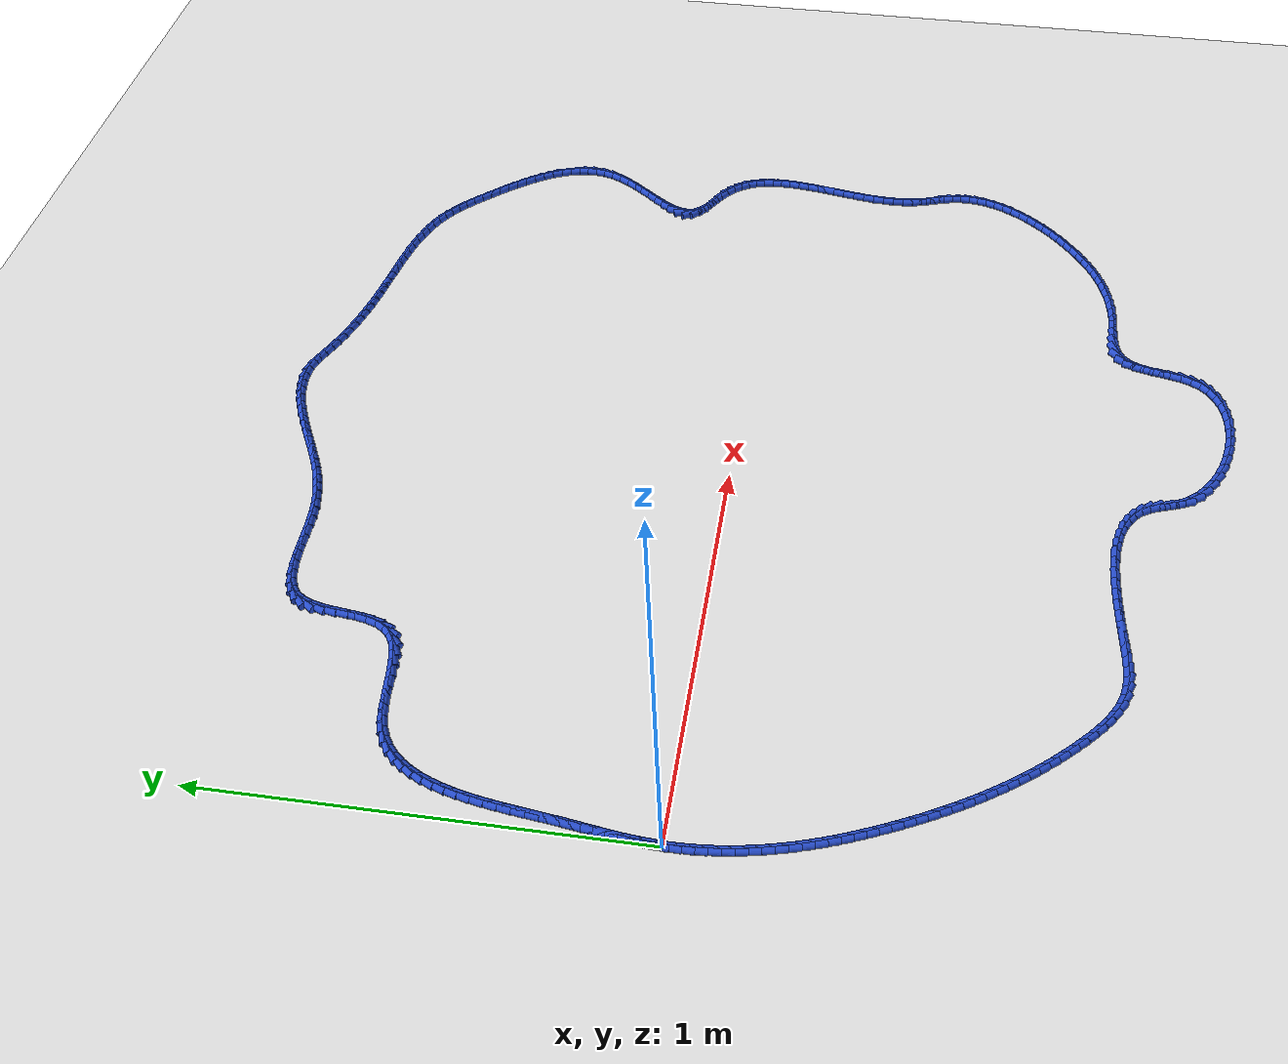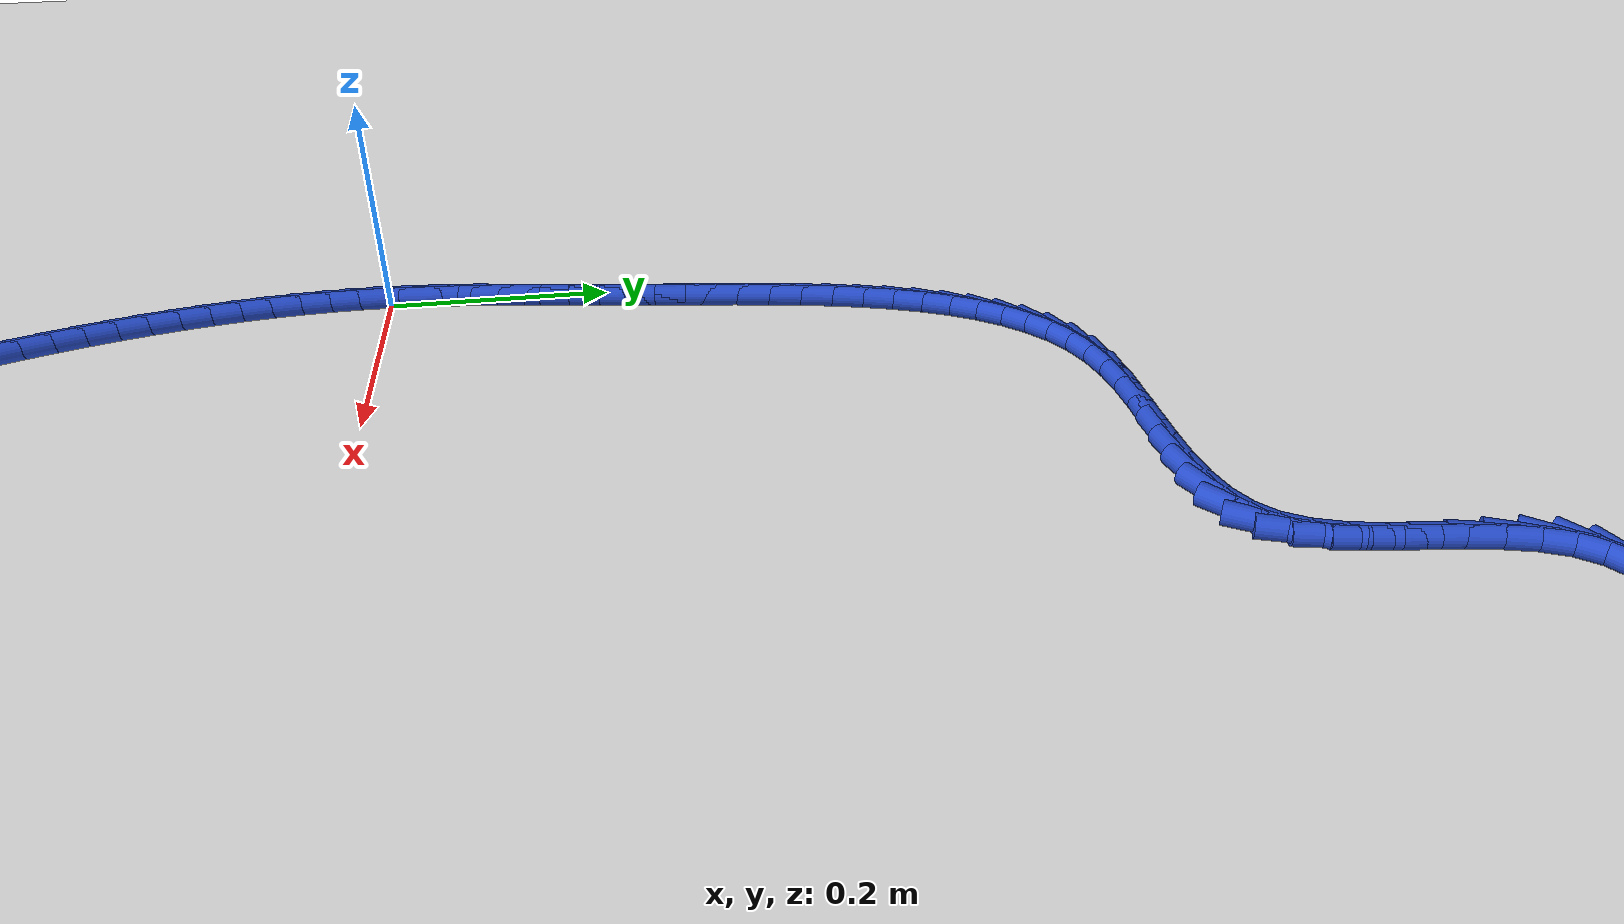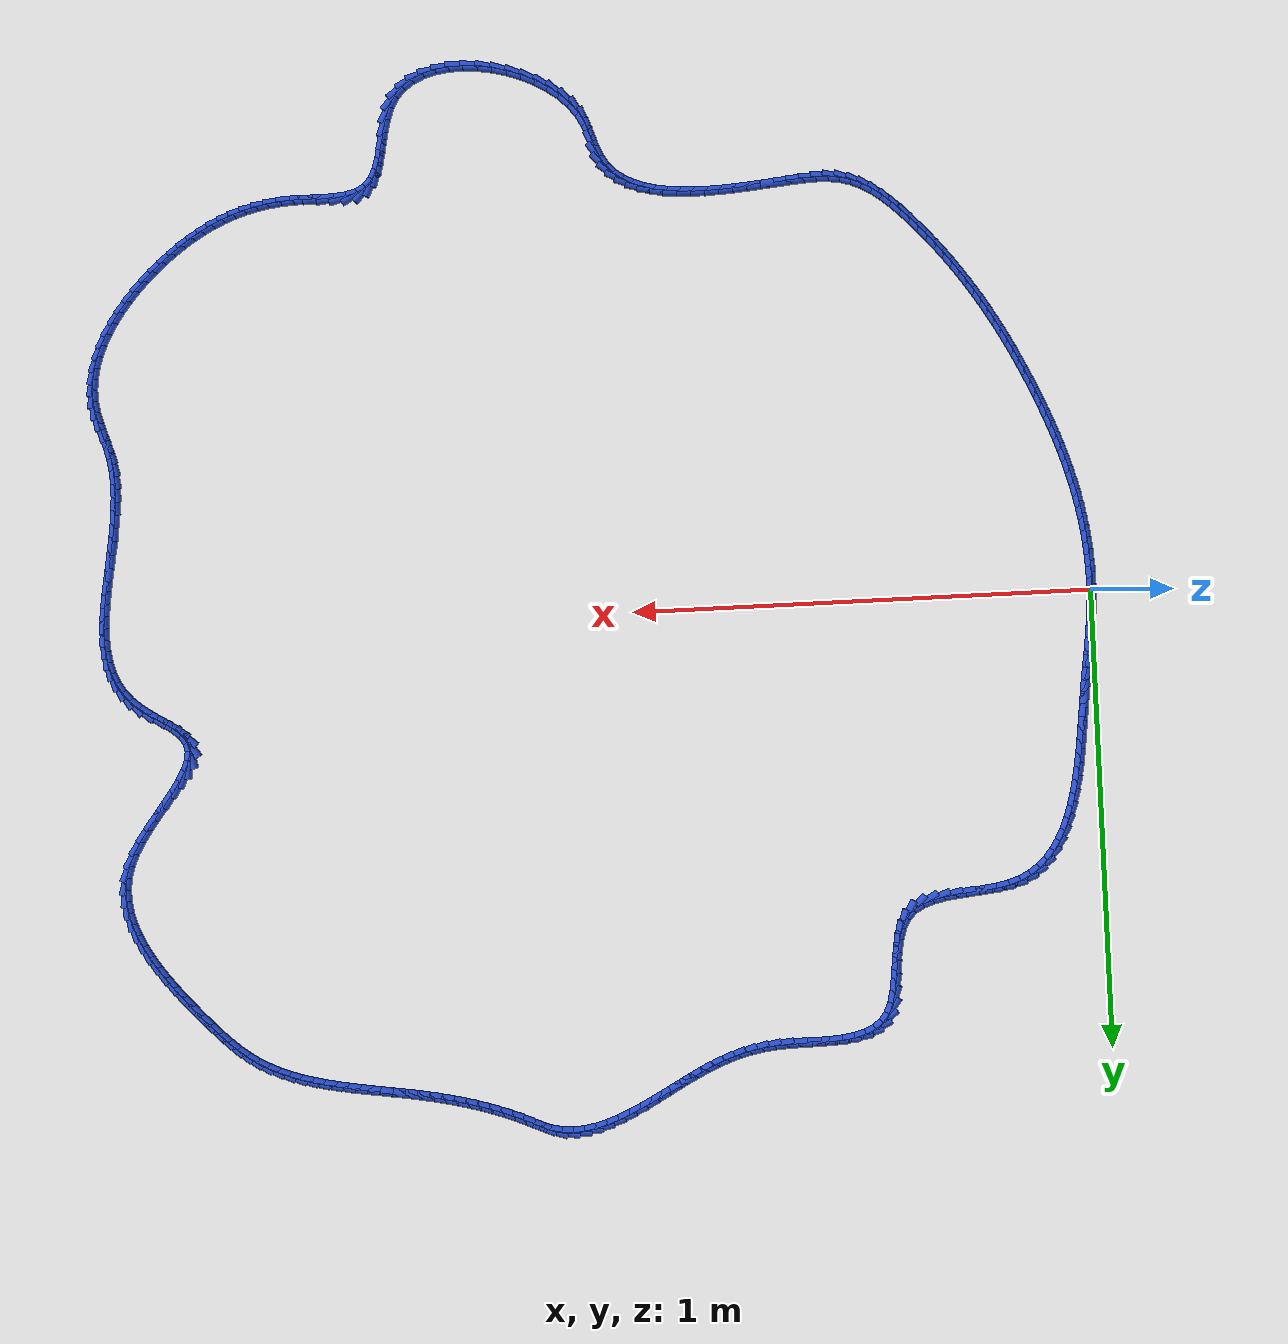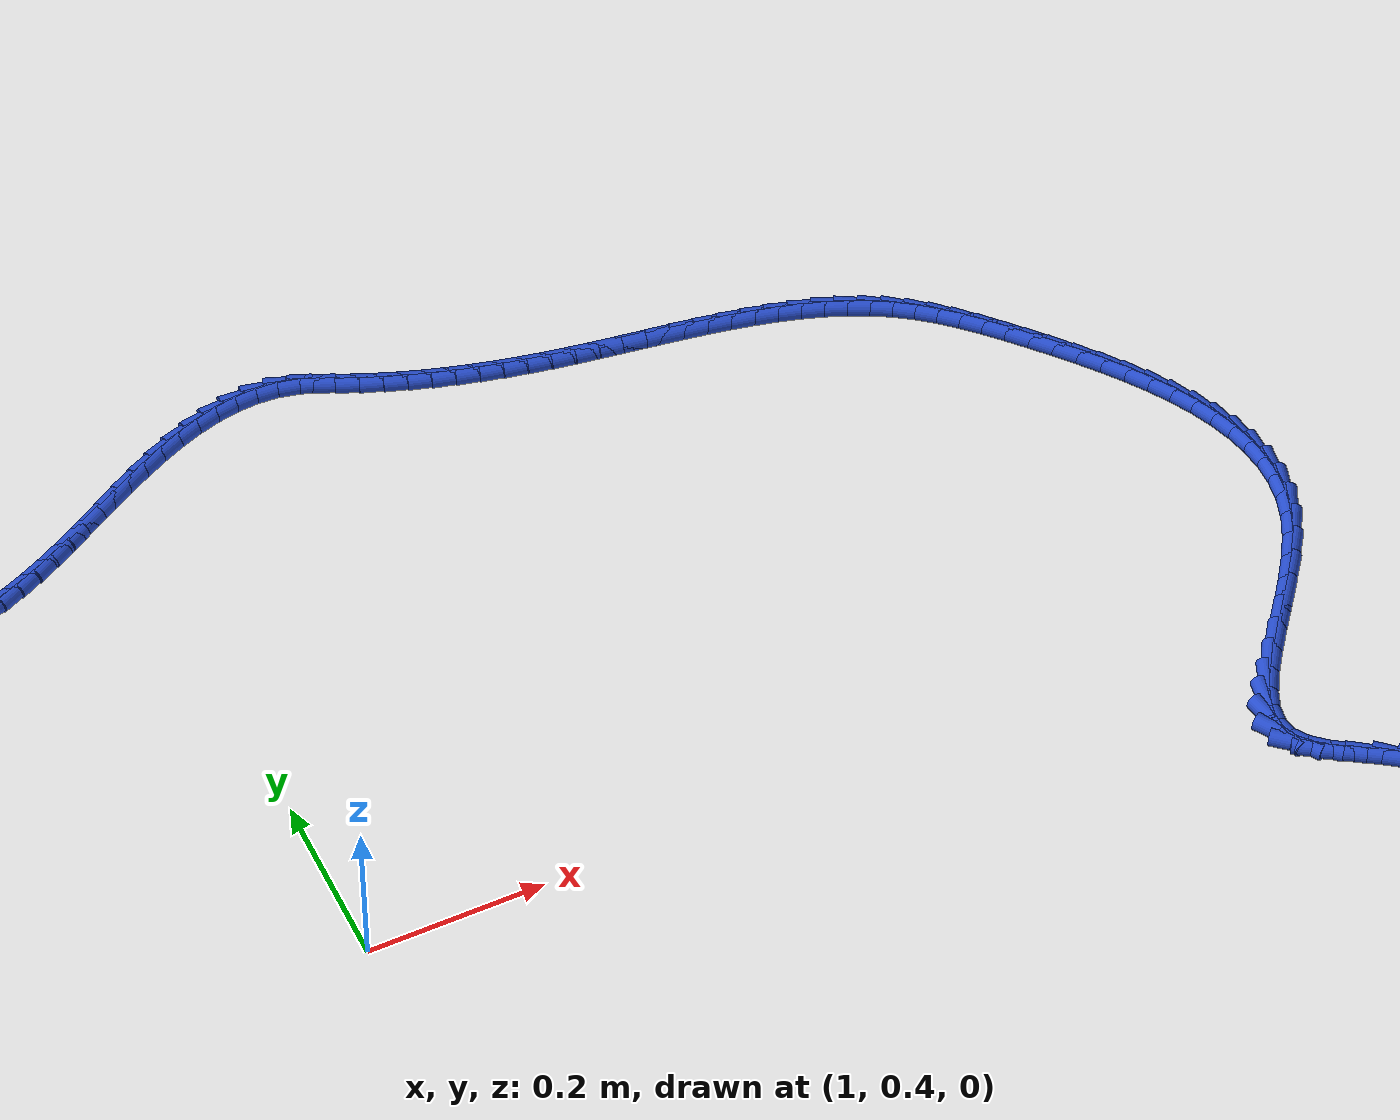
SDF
<sdf version="1.6">
 <world name="default">
  <light name="sun" type="directional">
   <pose>0 0 10 0 -0 0</pose>
   <diffuse>0.8 0.8 0.8 1</diffuse>
   <specular>0.2 0.2 0.2 1</specular>
   <attenuation>
    <range>1000</range>
    <constant>0.9</constant>
    <linear>0.01</linear>
    <quadratic>0.001</quadratic>
   </attenuation>
   <direction>-0.5 0.1 -0.9</direction>
  </light>
  <model name="ground_plane">
   <static>1</static>
   <link name="link">
    <collision name="collision">
     <geometry><plane><normal>0 0 1</normal><size>100 100</size></plane></geometry>
     <surface><friction><ode><mu>100</mu><mu2>50</mu2></ode></friction></surface>
    </collision>
    <visual name="visual">
     <cast_shadows>0</cast_shadows>
     <geometry><plane><normal>0 0 1</normal><size>100 100</size></plane></geometry>
     <material>
      <script><uri>file://media/materials/scripts/gazebo.material</uri><name>Gazebo/WhiteGlow</name></script>
     </material>
    </visual>
   </link>
  </model>
  <gravity>0 0 -9.8</gravity>
  <magnetic_field>6e-06 2.3e-05 -4.2e-05</magnetic_field>
  <atmosphere type="adiabatic"/>
  <physics name="default_physics" default="0" type="ode">
   <max_step_size>0.001</max_step_size>
   <real_time_factor>1</real_time_factor>
   <real_time_update_rate>1000</real_time_update_rate>
  </physics>
  <scene><ambient>0.4 0.4 0.4 1</ambient><background>0.7 0.7 0.7 1</background><shadows>1</shadows></scene>
  <spherical_coordinates>
   <surface_model>EARTH_WGS84</surface_model>
   <latitude_deg>0</latitude_deg>
   <longitude_deg>0</longitude_deg>
   <elevation>0</elevation>
   <heading_deg>0</heading_deg>
  </spherical_coordinates>
  <model name="line">
   <link name="link_0">
    <pose>-1.1275702593849246e-17 -2.0816681711721685e-17 0.01 0 1.57 1.5284242386121365</pose>
    <collision name="collision">
     <geometry><cylinder><radius>0.01</radius><length>0.08</length></cylinder></geometry>
    </collision>
    <visual name="visual">
     <material>
      <script><name>Gazebo/Blue</name><uri>file://media/materials/scripts/gazebo.material</uri></script>
     </material>
     <geometry><cylinder><radius>0.01</radius><length>0.08</length></cylinder></geometry>
    </visual>
   </link>
   <link name="link_1">
    <pose>0.0010763744634702198 0.025387708287615687 0.01 0 1.57 1.4976860426520275</pose>
    <collision name="collision">
     <geometry><cylinder><radius>0.01</radius><length>0.08</length></cylinder></geometry>
    </collision>
    <visual name="visual">
     <material>
      <script><name>Gazebo/Blue</name><uri>file://media/materials/scripts/gazebo.material</uri></script>
     </material>
     <geometry><cylinder><radius>0.01</radius><length>0.08</length></cylinder></geometry>
    </visual>
   </link>
   <link name="link_2">
    <pose>0.0029248905432477748 0.050626584291068956 0.01 0 1.57 1.4723690824219697</pose>
    <collision name="collision">
     <geometry><cylinder><radius>0.01</radius><length>0.08</length></cylinder></geometry>
    </collision>
    <visual name="visual">
     <material>
      <script><name>Gazebo/Blue</name><uri>file://media/materials/scripts/gazebo.material</uri></script>
     </material>
     <geometry><cylinder><radius>0.01</radius><length>0.08</length></cylinder></geometry>
    </visual>
   </link>
   <link name="link_3">
    <pose>0.005415936411598653 0.07585330206400076 0.01 0 1.57 1.4528524896862378</pose>
    <collision name="collision">
     <geometry><cylinder><radius>0.01</radius><length>0.08</length></cylinder></geometry>
    </collision>
    <visual name="visual">
     <material>
      <script><name>Gazebo/Blue</name><uri>file://media/materials/scripts/gazebo.material</uri></script>
     </material>
     <geometry><cylinder><radius>0.01</radius><length>0.08</length></cylinder></geometry>
    </visual>
   </link>
   <link name="link_4">
    <pose>0.008419900240788843 0.10120453566005193 0.01 0 1.57 1.4393083212164004</pose>
    <collision name="collision">
     <geometry><cylinder><radius>0.01</radius><length>0.08</length></cylinder></geometry>
    </collision>
    <visual name="visual">
     <material>
      <script><name>Gazebo/Blue</name><uri>file://media/materials/scripts/gazebo.material</uri></script>
     </material>
     <geometry><cylinder><radius>0.01</radius><length>0.08</length></cylinder></geometry>
    </visual>
   </link>
   <link name="link_5">
    <pose>0.011807170203084355 0.1268169591328635 0.01 0 1.57 1.4317183328385001</pose>
    <collision name="collision">
     <geometry><cylinder><radius>0.01</radius><length>0.08</length></cylinder></geometry>
    </collision>
    <visual name="visual">
     <material>
      <script><name>Gazebo/Blue</name><uri>file://media/materials/scripts/gazebo.material</uri></script>
     </material>
     <geometry><cylinder><radius>0.01</radius><length>0.08</length></cylinder></geometry>
    </visual>
   </link>
   <link name="link_6">
    <pose>0.015448134470751176 0.1528272465360764 0.01 0 1.57 1.4298988464182738</pose>
    <collision name="collision">
     <geometry><cylinder><radius>0.01</radius><length>0.08</length></cylinder></geometry>
    </collision>
    <visual name="visual">
     <material>
      <script><name>Gazebo/Blue</name><uri>file://media/materials/scripts/gazebo.material</uri></script>
     </material>
     <geometry><cylinder><radius>0.01</radius><length>0.08</length></cylinder></geometry>
    </visual>
   </link>
   <link name="link_7">
    <pose>0.019213181216055294 0.17937207192333138 0.01 0 1.57 1.433528916473025</pose>
    <collision name="collision">
     <geometry><cylinder><radius>0.01</radius><length>0.08</length></cylinder></geometry>
    </collision>
    <visual name="visual">
     <material>
      <script><name>Gazebo/Blue</name><uri>file://media/materials/scripts/gazebo.material</uri></script>
     </material>
     <geometry><cylinder><radius>0.01</radius><length>0.08</length></cylinder></geometry>
    </visual>
   </link>
   <link name="link_8">
    <pose>0.02297269861126272 0.20658810934826954 0.01 0 1.57 1.4420171696211461</pose>
    <collision name="collision">
     <geometry><cylinder><radius>0.01</radius><length>0.08</length></cylinder></geometry>
    </collision>
    <visual name="visual">
     <material>
      <script><name>Gazebo/Blue</name><uri>file://media/materials/scripts/gazebo.material</uri></script>
     </material>
     <geometry><cylinder><radius>0.01</radius><length>0.08</length></cylinder></geometry>
    </visual>
   </link>
   <link name="link_9">
    <pose>0.02660103614277419 0.2346070672586541 0.01 0 1.57 1.4497094799966588</pose>
    <collision name="collision">
     <geometry><cylinder><radius>0.01</radius><length>0.08</length></cylinder></geometry>
    </collision>
    <visual name="visual">
     <material>
      <script><name>Gazebo/Blue</name><uri>file://media/materials/scripts/gazebo.material</uri></script>
     </material>
     <geometry><cylinder><radius>0.01</radius><length>0.08</length></cylinder></geometry>
    </visual>
   </link>
   <link name="link_10">
    <pose>0.030104103244489547 0.26339574043311154 0.01 0 1.57 1.4505761143948817</pose>
    <collision name="collision">
     <geometry><cylinder><radius>0.01</radius><length>0.08</length></cylinder></geometry>
    </collision>
    <visual name="visual">
     <material>
      <script><name>Gazebo/Blue</name><uri>file://media/materials/scripts/gazebo.material</uri></script>
     </material>
     <geometry><cylinder><radius>0.01</radius><length>0.08</length></cylinder></geometry>
    </visual>
   </link>
   <link name="link_11">
    <pose>0.03364675740067169 0.2927216783124141 0.01 0 1.57 1.444638522972636</pose>
    <collision name="collision">
     <geometry><cylinder><radius>0.01</radius><length>0.08</length></cylinder></geometry>
    </collision>
    <visual name="visual">
     <material>
      <script><name>Gazebo/Blue</name><uri>file://media/materials/scripts/gazebo.material</uri></script>
     </material>
     <geometry><cylinder><radius>0.01</radius><length>0.08</length></cylinder></geometry>
    </visual>
   </link>
   <link name="link_12">
    <pose>0.03740335651491582 0.32234052132520546 0.01 0 1.57 1.431982470610407</pose>
    <collision name="collision">
     <geometry><cylinder><radius>0.01</radius><length>0.08</length></cylinder></geometry>
    </collision>
    <visual name="visual">
     <material>
      <script><name>Gazebo/Blue</name><uri>file://media/materials/scripts/gazebo.material</uri></script>
     </material>
     <geometry><cylinder><radius>0.01</radius><length>0.08</length></cylinder></geometry>
    </visual>
   </link>
   <link name="link_13">
    <pose>0.04154825849081716 0.35200790990012915 0.01 0 1.57 1.4124020818260645</pose>
    <collision name="collision">
     <geometry><cylinder><radius>0.01</radius><length>0.08</length></cylinder></geometry>
    </collision>
    <visual name="visual">
     <material>
      <script><name>Gazebo/Blue</name><uri>file://media/materials/scripts/gazebo.material</uri></script>
     </material>
     <geometry><cylinder><radius>0.01</radius><length>0.08</length></cylinder></geometry>
    </visual>
   </link>
   <link name="link_14">
    <pose>0.04625582123197092 0.3814794844658289 0.01 0 1.57 1.3854086551512816</pose>
    <collision name="collision">
     <geometry><cylinder><radius>0.01</radius><length>0.08</length></cylinder></geometry>
    </collision>
    <visual name="visual">
     <material>
      <script><name>Gazebo/Blue</name><uri>file://media/materials/scripts/gazebo.material</uri></script>
     </material>
     <geometry><cylinder><radius>0.01</radius><length>0.08</length></cylinder></geometry>
    </visual>
   </link>
   <link name="link_15">
    <pose>0.0517004026419723 0.4105108854509481 0.01 0 1.57 1.3502236417377473</pose>
    <collision name="collision">
     <geometry><cylinder><radius>0.01</radius><length>0.08</length></cylinder></geometry>
    </collision>
    <visual name="visual">
     <material>
      <script><name>Gazebo/Blue</name><uri>file://media/materials/scripts/gazebo.material</uri></script>
     </material>
     <geometry><cylinder><radius>0.01</radius><length>0.08</length></cylinder></geometry>
    </visual>
   </link>
   <link name="link_16">
    <pose>0.058056360624416554 0.43885775328413046 0.01 0 1.57 1.3057646551096538</pose>
    <collision name="collision">
     <geometry><cylinder><radius>0.01</radius><length>0.08</length></cylinder></geometry>
    </collision>
    <visual name="visual">
     <material>
      <script><name>Gazebo/Blue</name><uri>file://media/materials/scripts/gazebo.material</uri></script>
     </material>
     <geometry><cylinder><radius>0.01</radius><length>0.08</length></cylinder></geometry>
    </visual>
   </link>
   <link name="link_17">
    <pose>0.06549805308289884 0.4662757283940195 0.01 0 1.57 1.250639718339587</pose>
    <collision name="collision">
     <geometry><cylinder><radius>0.01</radius><length>0.08</length></cylinder></geometry>
    </collision>
    <visual name="visual">
     <material>
      <script><name>Gazebo/Blue</name><uri>file://media/materials/scripts/gazebo.material</uri></script>
     </material>
     <geometry><cylinder><radius>0.01</radius><length>0.08</length></cylinder></geometry>
    </visual>
   </link>
   <link name="link_18">
    <pose>0.0741998379210144 0.4925204512092588 0.01 0 1.57 1.1831785969941981</pose>
    <collision name="collision">
     <geometry><cylinder><radius>0.01</radius><length>0.08</length></cylinder></geometry>
    </collision>
    <visual name="visual">
     <material>
      <script><name>Gazebo/Blue</name><uri>file://media/materials/scripts/gazebo.material</uri></script>
     </material>
     <geometry><cylinder><radius>0.01</radius><length>0.08</length></cylinder></geometry>
    </visual>
   </link>
   <link name="link_19">
    <pose>0.08433607304235843 0.517347562158492 0.01 0 1.57 1.1015535062578246</pose>
    <collision name="collision">
     <geometry><cylinder><radius>0.01</radius><length>0.08</length></cylinder></geometry>
    </collision>
    <visual name="visual">
     <material>
      <script><name>Gazebo/Blue</name><uri>file://media/materials/scripts/gazebo.material</uri></script>
     </material>
     <geometry><cylinder><radius>0.01</radius><length>0.08</length></cylinder></geometry>
    </visual>
   </link>
   <link name="link_20">
    <pose>0.09608111635052617 0.5405127016703627 0.01 0 1.57 1.004071236986781</pose>
    <collision name="collision">
     <geometry><cylinder><radius>0.01</radius><length>0.08</length></cylinder></geometry>
    </collision>
    <visual name="visual">
     <material>
      <script><name>Gazebo/Blue</name><uri>file://media/materials/scripts/gazebo.material</uri></script>
     </material>
     <geometry><cylinder><radius>0.01</radius><length>0.08</length></cylinder></geometry>
    </visual>
   </link>
   <link name="link_21">
    <pose>0.10960932574911281 0.5617715101735143 0.01 0 1.57 0.8897297578428682</pose>
    <collision name="collision">
     <geometry><cylinder><radius>0.01</radius><length>0.08</length></cylinder></geometry>
    </collision>
    <visual name="visual">
     <material>
      <script><name>Gazebo/Blue</name><uri>file://media/materials/scripts/gazebo.material</uri></script>
     </material>
     <geometry><cylinder><radius>0.01</radius><length>0.08</length></cylinder></geometry>
    </visual>
   </link>
   <link name="link_22">
    <pose>0.1250950591417136 0.5808796280965908 0.01 0 1.57 0.7590561798899498</pose>
    <collision name="collision">
     <geometry><cylinder><radius>0.01</radius><length>0.08</length></cylinder></geometry>
    </collision>
    <visual name="visual">
     <material>
      <script><name>Gazebo/Blue</name><uri>file://media/materials/scripts/gazebo.material</uri></script>
     </material>
     <geometry><cylinder><radius>0.01</radius><length>0.08</length></cylinder></geometry>
    </visual>
   </link>
   <link name="link_23">
    <pose>0.1427126744319237 0.5975926958682354 0.01 0 1.57 0.6149898415633533</pose>
    <collision name="collision">
     <geometry><cylinder><radius>0.01</radius><length>0.08</length></cylinder></geometry>
    </collision>
    <visual name="visual">
     <material>
      <script><name>Gazebo/Blue</name><uri>file://media/materials/scripts/gazebo.material</uri></script>
     </material>
     <geometry><cylinder><radius>0.01</radius><length>0.08</length></cylinder></geometry>
    </visual>
   </link>
   <link name="link_24">
    <pose>0.1626365295233383 0.6116663539170916 0.01 0 1.57 0.4632069694213006</pose>
    <collision name="collision">
     <geometry><cylinder><radius>0.01</radius><length>0.08</length></cylinder></geometry>
    </collision>
    <visual name="visual">
     <material>
      <script><name>Gazebo/Blue</name><uri>file://media/materials/scripts/gazebo.material</uri></script>
     </material>
     <geometry><cylinder><radius>0.01</radius><length>0.08</length></cylinder></geometry>
    </visual>
   </link>
   <link name="link_25">
    <pose>0.18504098231955268 0.6228562426718033 0.01 0 1.57 0.3150501466540137</pose>
    <collision name="collision">
     <geometry><cylinder><radius>0.01</radius><length>0.08</length></cylinder></geometry>
    </collision>
    <visual name="visual">
     <material>
      <script><name>Gazebo/Blue</name><uri>file://media/materials/scripts/gazebo.material</uri></script>
     </material>
     <geometry><cylinder><radius>0.01</radius><length>0.08</length></cylinder></geometry>
    </visual>
   </link>
   <link name="link_26">
    <pose>0.2100290350860774 0.6309999719050797 0.01 0 1.57 0.20433990257603554</pose>
    <collision name="collision">
     <geometry><cylinder><radius>0.01</radius><length>0.08</length></cylinder></geometry>
    </collision>
    <visual name="visual">
     <material>
      <script><name>Gazebo/Blue</name><uri>file://media/materials/scripts/gazebo.material</uri></script>
     </material>
     <geometry><cylinder><radius>0.01</radius><length>0.08</length></cylinder></geometry>
    </visual>
   </link>
   <link name="link_27">
    <pose>0.23711378121506127 0.6366128055274946 0.01 0 1.57 0.13754254039878605</pose>
    <collision name="collision">
     <geometry><cylinder><radius>0.01</radius><length>0.08</length></cylinder></geometry>
    </collision>
    <visual name="visual">
     <material>
      <script><name>Gazebo/Blue</name><uri>file://media/materials/scripts/gazebo.material</uri></script>
     </material>
     <geometry><cylinder><radius>0.01</radius><length>0.08</length></cylinder></geometry>
    </visual>
   </link>
   <link name="link_28">
    <pose>0.2655172899207083 0.6405443196583519 0.01 0 1.57 0.10677552042237404</pose>
    <collision name="collision">
     <geometry><cylinder><radius>0.01</radius><length>0.08</length></cylinder></geometry>
    </collision>
    <visual name="visual">
     <material>
      <script><name>Gazebo/Blue</name><uri>file://media/materials/scripts/gazebo.material</uri></script>
     </material>
     <geometry><cylinder><radius>0.01</radius><length>0.08</length></cylinder></geometry>
    </visual>
   </link>
   <link name="link_29">
    <pose>0.2944595799850303 0.6436464458381436 0.01 0 1.57 0.10844228253412252</pose>
    <collision name="collision">
     <geometry><cylinder><radius>0.01</radius><length>0.08</length></cylinder></geometry>
    </collision>
    <visual name="visual">
     <material>
      <script><name>Gazebo/Blue</name><uri>file://media/materials/scripts/gazebo.material</uri></script>
     </material>
     <geometry><cylinder><radius>0.01</radius><length>0.08</length></cylinder></geometry>
    </visual>
   </link>
   <link name="link_30">
    <pose>0.3231606701900389 0.6467711156073614 0.01 0 1.57 0.1434853802040433</pose>
    <collision name="collision">
     <geometry><cylinder><radius>0.01</radius><length>0.08</length></cylinder></geometry>
    </collision>
    <visual name="visual">
     <material>
      <script><name>Gazebo/Blue</name><uri>file://media/materials/scripts/gazebo.material</uri></script>
     </material>
     <geometry><cylinder><radius>0.01</radius><length>0.08</length></cylinder></geometry>
    </visual>
   </link>
   <link name="link_31">
    <pose>0.35084057931774626 0.6507702605064981 0.01 0 1.57 0.21773782115448276</pose>
    <collision name="collision">
     <geometry><cylinder><radius>0.01</radius><length>0.08</length></cylinder></geometry>
    </collision>
    <visual name="visual">
     <material>
      <script><name>Gazebo/Blue</name><uri>file://media/materials/scripts/gazebo.material</uri></script>
     </material>
     <geometry><cylinder><radius>0.01</radius><length>0.08</length></cylinder></geometry>
    </visual>
   </link>
   <link name="link_32">
    <pose>0.37671932615016385 0.6564958120760451 0.01 0 1.57 0.34238872530657055</pose>
    <collision name="collision">
     <geometry><cylinder><radius>0.01</radius><length>0.08</length></cylinder></geometry>
    </collision>
    <visual name="visual">
     <material>
      <script><name>Gazebo/Blue</name><uri>file://media/materials/scripts/gazebo.material</uri></script>
     </material>
     <geometry><cylinder><radius>0.01</radius><length>0.08</length></cylinder></geometry>
    </visual>
   </link>
   <link name="link_33">
    <pose>0.4000169294693037 0.6647997018564946 0.01 0 1.57 0.5319781454603224</pose>
    <collision name="collision">
     <geometry><cylinder><radius>0.01</radius><length>0.08</length></cylinder></geometry>
    </collision>
    <visual name="visual">
     <material>
      <script><name>Gazebo/Blue</name><uri>file://media/materials/scripts/gazebo.material</uri></script>
     </material>
     <geometry><cylinder><radius>0.01</radius><length>0.08</length></cylinder></geometry>
    </visual>
   </link>
   <link name="link_34">
    <pose>0.4199534080571775 0.6765338613883385 0.01 0 1.57 0.7923177625287058</pose>
    <collision name="collision">
     <geometry><cylinder><radius>0.01</radius><length>0.08</length></cylinder></geometry>
    </collision>
    <visual name="visual">
     <material>
      <script><name>Gazebo/Blue</name><uri>file://media/materials/scripts/gazebo.material</uri></script>
     </material>
     <geometry><cylinder><radius>0.01</radius><length>0.08</length></cylinder></geometry>
    </visual>
   </link>
   <link name="link_35">
    <pose>0.43574919612393337 0.6925497772069762 0.01 0 1.57 1.070897125102758</pose>
    <collision name="collision">
     <geometry><cylinder><radius>0.01</radius><length>0.08</length></cylinder></geometry>
    </collision>
    <visual name="visual">
     <material>
      <script><name>Gazebo/Blue</name><uri>file://media/materials/scripts/gazebo.material</uri></script>
     </material>
     <geometry><cylinder><radius>0.01</radius><length>0.08</length></cylinder></geometry>
    </visual>
   </link>
   <link name="link_36">
    <pose>0.4470509197334005 0.7132424007002299 0.01 0 1.57 1.2662341445706322</pose>
    <collision name="collision">
     <geometry><cylinder><radius>0.01</radius><length>0.08</length></cylinder></geometry>
    </collision>
    <visual name="visual">
     <material>
      <script><name>Gazebo/Blue</name><uri>file://media/materials/scripts/gazebo.material</uri></script>
     </material>
     <geometry><cylinder><radius>0.01</radius><length>0.08</length></cylinder></geometry>
    </visual>
   </link>
   <link name="link_37">
    <pose>0.45473546291214306 0.7376888354469547 0.01 0 1.57 1.3820660804485176</pose>
    <collision name="collision">
     <geometry><cylinder><radius>0.01</radius><length>0.08</length></cylinder></geometry>
    </collision>
    <visual name="visual">
     <material>
      <script><name>Gazebo/Blue</name><uri>file://media/materials/scripts/gazebo.material</uri></script>
     </material>
     <geometry><cylinder><radius>0.01</radius><length>0.08</length></cylinder></geometry>
    </visual>
   </link>
   <link name="link_38">
    <pose>0.45990038074570133 0.7647298029985087 0.01 0 1.57 1.44010782992766</pose>
    <collision name="collision">
     <geometry><cylinder><radius>0.01</radius><length>0.08</length></cylinder></geometry>
    </collision>
    <visual name="visual">
     <material>
      <script><name>Gazebo/Blue</name><uri>file://media/materials/scripts/gazebo.material</uri></script>
     </material>
     <geometry><cylinder><radius>0.01</radius><length>0.08</length></cylinder></geometry>
    </visual>
   </link>
   <link name="link_39">
    <pose>0.4636432283196159 0.7932060249062507 0.01 0 1.57 1.452462349332815</pose>
    <collision name="collision">
     <geometry><cylinder><radius>0.01</radius><length>0.08</length></cylinder></geometry>
    </collision>
    <visual name="visual">
     <material>
      <script><name>Gazebo/Blue</name><uri>file://media/materials/scripts/gazebo.material</uri></script>
     </material>
     <geometry><cylinder><radius>0.01</radius><length>0.08</length></cylinder></geometry>
    </visual>
   </link>
   <link name="link_40">
    <pose>0.4670615607194273 0.8219582227215383 0.01 0 1.57 1.4215190476510389</pose>
    <collision name="collision">
     <geometry><cylinder><radius>0.01</radius><length>0.08</length></cylinder></geometry>
    </collision>
    <visual name="visual">
     <material>
      <script><name>Gazebo/Blue</name><uri>file://media/materials/scripts/gazebo.material</uri></script>
     </material>
     <geometry><cylinder><radius>0.01</radius><length>0.08</length></cylinder></geometry>
    </visual>
   </link>
   <link name="link_41">
    <pose>0.4712529330306759 0.8498271179957307 0.01 0 1.57 1.3402491853394312</pose>
    <collision name="collision">
     <geometry><cylinder><radius>0.01</radius><length>0.08</length></cylinder></geometry>
    </collision>
    <visual name="visual">
     <material>
      <script><name>Gazebo/Blue</name><uri>file://media/materials/scripts/gazebo.material</uri></script>
     </material>
     <geometry><cylinder><radius>0.01</radius><length>0.08</length></cylinder></geometry>
    </visual>
   </link>
   <link name="link_42">
    <pose>0.477314900338902 0.8756534322801854 0.01 0 1.57 1.1910394605796708</pose>
    <collision name="collision">
     <geometry><cylinder><radius>0.01</radius><length>0.08</length></cylinder></geometry>
    </collision>
    <visual name="visual">
     <material>
      <script><name>Gazebo/Blue</name><uri>file://media/materials/scripts/gazebo.material</uri></script>
     </material>
     <geometry><cylinder><radius>0.01</radius><length>0.08</length></cylinder></geometry>
    </visual>
   </link>
   <link name="link_43">
    <pose>0.48634501772964633 0.8982778871262612 0.01 0 1.57 0.9505667504201235</pose>
    <collision name="collision">
     <geometry><cylinder><radius>0.01</radius><length>0.08</length></cylinder></geometry>
    </collision>
    <visual name="visual">
     <material>
      <script><name>Gazebo/Blue</name><uri>file://media/materials/scripts/gazebo.material</uri></script>
     </material>
     <geometry><cylinder><radius>0.01</radius><length>0.08</length></cylinder></geometry>
    </visual>
   </link>
   <link name="link_44">
    <pose>0.49941183105960485 0.9165721958688583 0.01 0 1.57 0.6671425733829582</pose>
    <collision name="collision">
     <geometry><cylinder><radius>0.01</radius><length>0.08</length></cylinder></geometry>
    </collision>
    <visual name="visual">
     <material>
      <script><name>Gazebo/Blue</name><uri>file://media/materials/scripts/gazebo.material</uri></script>
     </material>
     <geometry><cylinder><radius>0.01</radius><length>0.08</length></cylinder></geometry>
    </visual>
   </link>
   <link name="link_45">
    <pose>0.5167882400707897 0.9302580941683474 0.01 0 1.57 0.43248300576456994</pose>
    <collision name="collision">
     <geometry><cylinder><radius>0.01</radius><length>0.08</length></cylinder></geometry>
    </collision>
    <visual name="visual">
     <material>
      <script><name>Gazebo/Blue</name><uri>file://media/materials/scripts/gazebo.material</uri></script>
     </material>
     <geometry><cylinder><radius>0.01</radius><length>0.08</length></cylinder></geometry>
    </visual>
   </link>
   <link name="link_46">
    <pose>0.5378728412767588 0.9399913727250232 0.01 0 1.57 0.26234919527058076</pose>
    <collision name="collision">
     <geometry><cylinder><radius>0.01</radius><length>0.08</length></cylinder></geometry>
    </collision>
    <visual name="visual">
     <material>
      <script><name>Gazebo/Blue</name><uri>file://media/materials/scripts/gazebo.material</uri></script>
     </material>
     <geometry><cylinder><radius>0.01</radius><length>0.08</length></cylinder></geometry>
    </visual>
   </link>
   <link name="link_47">
    <pose>0.5620194466986577 0.9464756674026049 0.01 0 1.57 0.14721734777549855</pose>
    <collision name="collision">
     <geometry><cylinder><radius>0.01</radius><length>0.08</length></cylinder></geometry>
    </collision>
    <visual name="visual">
     <material>
      <script><name>Gazebo/Blue</name><uri>file://media/materials/scripts/gazebo.material</uri></script>
     </material>
     <geometry><cylinder><radius>0.01</radius><length>0.08</length></cylinder></geometry>
    </visual>
   </link>
   <link name="link_48">
    <pose>0.5885818683576327 0.9504146140648114 0.01 0 1.57 0.07388863454450137</pose>
    <collision name="collision">
     <geometry><cylinder><radius>0.01</radius><length>0.08</length></cylinder></geometry>
    </collision>
    <visual name="visual">
     <material>
      <script><name>Gazebo/Blue</name><uri>file://media/materials/scripts/gazebo.material</uri></script>
     </material>
     <geometry><cylinder><radius>0.01</radius><length>0.08</length></cylinder></geometry>
    </visual>
   </link>
   <link name="link_49">
    <pose>0.6169139182748291 0.9525118485753619 0.01 0 1.57 0.0325514672555364</pose>
    <collision name="collision">
     <geometry><cylinder><radius>0.01</radius><length>0.08</length></cylinder></geometry>
    </collision>
    <visual name="visual">
     <material>
      <script><name>Gazebo/Blue</name><uri>file://media/materials/scripts/gazebo.material</uri></script>
     </material>
     <geometry><cylinder><radius>0.01</radius><length>0.08</length></cylinder></geometry>
    </visual>
   </link>
   <link name="link_50">
    <pose>0.6463694084713933 0.9534710067979758 0.01 0 1.57 0.017528098544785757</pose>
    <collision name="collision">
     <geometry><cylinder><radius>0.01</radius><length>0.08</length></cylinder></geometry>
    </collision>
    <visual name="visual">
     <material>
      <script><name>Gazebo/Blue</name><uri>file://media/materials/scripts/gazebo.material</uri></script>
     </material>
     <geometry><cylinder><radius>0.01</radius><length>0.08</length></cylinder></geometry>
    </visual>
   </link>
   <link name="link_51">
    <pose>0.6763021509684706 0.953995724596372 0.01 0 1.57 0.026667456747574873</pose>
    <collision name="collision">
     <geometry><cylinder><radius>0.01</radius><length>0.08</length></cylinder></geometry>
    </collision>
    <visual name="visual">
     <material>
      <script><name>Gazebo/Blue</name><uri>file://media/materials/scripts/gazebo.material</uri></script>
     </material>
     <geometry><cylinder><radius>0.01</radius><length>0.08</length></cylinder></geometry>
    </visual>
   </link>
   <link name="link_52">
    <pose>0.7060659577872074 0.95478963783427 0.01 0 1.57 0.06095461739545288</pose>
    <collision name="collision">
     <geometry><cylinder><radius>0.01</radius><length>0.08</length></cylinder></geometry>
    </collision>
    <visual name="visual">
     <material>
      <script><name>Gazebo/Blue</name><uri>file://media/materials/scripts/gazebo.material</uri></script>
     </material>
     <geometry><cylinder><radius>0.01</radius><length>0.08</length></cylinder></geometry>
    </visual>
   </link>
   <link name="link_53">
    <pose>0.7350146409487491 0.9565563823753883 0.01 0 1.57 0.1211702622609101</pose>
    <collision name="collision">
     <geometry><cylinder><radius>0.01</radius><length>0.08</length></cylinder></geometry>
    </collision>
    <visual name="visual">
     <material>
      <script><name>Gazebo/Blue</name><uri>file://media/materials/scripts/gazebo.material</uri></script>
     </material>
     <geometry><cylinder><radius>0.01</radius><length>0.08</length></cylinder></geometry>
    </visual>
   </link>
   <link name="link_54">
    <pose>0.762596069342792 0.9599148841665189 0.01 0 1.57 0.1895481863788539</pose>
    <collision name="collision">
     <geometry><cylinder><radius>0.01</radius><length>0.08</length></cylinder></geometry>
    </collision>
    <visual name="visual">
     <material>
      <script><name>Gazebo/Blue</name><uri>file://media/materials/scripts/gazebo.material</uri></script>
     </material>
     <geometry><cylinder><radius>0.01</radius><length>0.08</length></cylinder></geometry>
    </visual>
   </link>
   <link name="link_55">
    <pose>0.7888493262262767 0.9649516070311946 0.01 0 1.57 0.2560312832328813</pose>
    <collision name="collision">
     <geometry><cylinder><radius>0.01</radius><length>0.08</length></cylinder></geometry>
    </collision>
    <visual name="visual">
     <material>
      <script><name>Gazebo/Blue</name><uri>file://media/materials/scripts/gazebo.material</uri></script>
     </material>
     <geometry><cylinder><radius>0.01</radius><length>0.08</length></cylinder></geometry>
    </visual>
   </link>
   <link name="link_56">
    <pose>0.8140426557753861 0.9715466268626329 0.01 0 1.57 0.3180168319167051</pose>
    <collision name="collision">
     <geometry><cylinder><radius>0.01</radius><length>0.08</length></cylinder></geometry>
    </collision>
    <visual name="visual">
     <material>
      <script><name>Gazebo/Blue</name><uri>file://media/materials/scripts/gazebo.material</uri></script>
     </material>
     <geometry><cylinder><radius>0.01</radius><length>0.08</length></cylinder></geometry>
    </visual>
   </link>
   <link name="link_57">
    <pose>0.8384448041861334 0.9795795674227095 0.01 0 1.57 0.3732146522069759</pose>
    <collision name="collision">
     <geometry><cylinder><radius>0.01</radius><length>0.08</length></cylinder></geometry>
    </collision>
    <visual name="visual">
     <material>
      <script><name>Gazebo/Blue</name><uri>file://media/materials/scripts/gazebo.material</uri></script>
     </material>
     <geometry><cylinder><radius>0.01</radius><length>0.08</length></cylinder></geometry>
    </visual>
   </link>
   <link name="link_58">
    <pose>0.8623245176545319 0.9889300524733017 0.01 0 1.57 0.41989128030626427</pose>
    <collision name="collision">
     <geometry><cylinder><radius>0.01</radius><length>0.08</length></cylinder></geometry>
    </collision>
    <visual name="visual">
     <material>
      <script><name>Gazebo/Blue</name><uri>file://media/materials/scripts/gazebo.material</uri></script>
     </material>
     <geometry><cylinder><radius>0.01</radius><length>0.08</length></cylinder></geometry>
    </visual>
   </link>
   <link name="link_59">
    <pose>0.8859505423765944 0.9994777057762855 0.01 0 1.57 0.45698985455259017</pose>
    <collision name="collision">
     <geometry><cylinder><radius>0.01</radius><length>0.08</length></cylinder></geometry>
    </collision>
    <visual name="visual">
     <material>
      <script><name>Gazebo/Blue</name><uri>file://media/materials/scripts/gazebo.material</uri></script>
     </material>
     <geometry><cylinder><radius>0.01</radius><length>0.08</length></cylinder></geometry>
    </visual>
   </link>
   <link name="link_60">
    <pose>0.9095916245483342 1.0111021510935374 0.01 0 1.57 0.48405005360047765</pose>
    <collision name="collision">
     <geometry><cylinder><radius>0.01</radius><length>0.08</length></cylinder></geometry>
    </collision>
    <visual name="visual">
     <material>
      <script><name>Gazebo/Blue</name><uri>file://media/materials/scripts/gazebo.material</uri></script>
     </material>
     <geometry><cylinder><radius>0.01</radius><length>0.08</length></cylinder></geometry>
    </visual>
   </link>
   <link name="link_61">
    <pose>0.9335106483913236 1.0236780445863247 0.01 0 1.57 0.49978914174198985</pose>
    <collision name="collision">
     <geometry><cylinder><radius>0.01</radius><length>0.08</length></cylinder></geometry>
    </collision>
    <visual name="visual">
     <material>
      <script><name>Gazebo/Blue</name><uri>file://media/materials/scripts/gazebo.material</uri></script>
     </material>
     <geometry><cylinder><radius>0.01</radius><length>0.08</length></cylinder></geometry>
    </visual>
   </link>
   <link name="link_62">
    <pose>0.9578171564107384 1.0369500963693181 0.01 0 1.57 0.5035309886041415</pose>
    <collision name="collision">
     <geometry><cylinder><radius>0.01</radius><length>0.08</length></cylinder></geometry>
    </collision>
    <visual name="visual">
     <material>
      <script><name>Gazebo/Blue</name><uri>file://media/materials/scripts/gazebo.material</uri></script>
     </material>
     <geometry><cylinder><radius>0.01</radius><length>0.08</length></cylinder></geometry>
    </visual>
   </link>
   <link name="link_63">
    <pose>0.9824562974679931 1.0505237047991474 0.01 0 1.57 0.49584609794629053</pose>
    <collision name="collision">
     <geometry><cylinder><radius>0.01</radius><length>0.08</length></cylinder></geometry>
    </collision>
    <visual name="visual">
     <material>
      <script><name>Gazebo/Blue</name><uri>file://media/materials/scripts/gazebo.material</uri></script>
     </material>
     <geometry><cylinder><radius>0.01</radius><length>0.08</length></cylinder></geometry>
    </visual>
   </link>
   <link name="link_64">
    <pose>1.0073651447079515 1.0639974246450357 0.01 0 1.57 0.4767654918591282</pose>
    <collision name="collision">
     <geometry><cylinder><radius>0.01</radius><length>0.08</length></cylinder></geometry>
    </collision>
    <visual name="visual">
     <material>
      <script><name>Gazebo/Blue</name><uri>file://media/materials/scripts/gazebo.material</uri></script>
     </material>
     <geometry><cylinder><radius>0.01</radius><length>0.08</length></cylinder></geometry>
    </visual>
   </link>
   <link name="link_65">
    <pose>1.0324807712754778 1.0769698106762067 0.01 0 1.57 0.4457506424002705</pose>
    <collision name="collision">
     <geometry><cylinder><radius>0.01</radius><length>0.08</length></cylinder></geometry>
    </collision>
    <visual name="visual">
     <material>
      <script><name>Gazebo/Blue</name><uri>file://media/materials/scripts/gazebo.material</uri></script>
     </material>
     <geometry><cylinder><radius>0.01</radius><length>0.08</length></cylinder></geometry>
    </visual>
   </link>
   <link name="link_66">
    <pose>1.057740250315437 1.0890394176618845 0.01 0 1.57 0.401727268846649</pose>
    <collision name="collision">
     <geometry><cylinder><radius>0.01</radius><length>0.08</length></cylinder></geometry>
    </collision>
    <visual name="visual">
     <material>
      <script><name>Gazebo/Blue</name><uri>file://media/materials/scripts/gazebo.material</uri></script>
     </material>
     <geometry><cylinder><radius>0.01</radius><length>0.08</length></cylinder></geometry>
    </visual>
   </link>
   <link name="link_67">
    <pose>1.0830806549726932 1.099804800371293 0.01 0 1.57 0.3431337729338121</pose>
    <collision name="collision">
     <geometry><cylinder><radius>0.01</radius><length>0.08</length></cylinder></geometry>
    </collision>
    <visual name="visual">
     <material>
      <script><name>Gazebo/Blue</name><uri>file://media/materials/scripts/gazebo.material</uri></script>
     </material>
     <geometry><cylinder><radius>0.01</radius><length>0.08</length></cylinder></geometry>
    </visual>
   </link>
   <link name="link_68">
    <pose>1.1084390583921109 1.1088645135736555 0.01 0 1.57 0.26805006358286426</pose>
    <collision name="collision">
     <geometry><cylinder><radius>0.01</radius><length>0.08</length></cylinder></geometry>
    </collision>
    <visual name="visual">
     <material>
      <script><name>Gazebo/Blue</name><uri>file://media/materials/scripts/gazebo.material</uri></script>
     </material>
     <geometry><cylinder><radius>0.01</radius><length>0.08</length></cylinder></geometry>
    </visual>
   </link>
   <link name="link_69">
    <pose>1.1337525337185546 1.1158171120381963 0.01 0 1.57 0.1745178250083528</pose>
    <collision name="collision">
     <geometry><cylinder><radius>0.01</radius><length>0.08</length></cylinder></geometry>
    </collision>
    <visual name="visual">
     <material>
      <script><name>Gazebo/Blue</name><uri>file://media/materials/scripts/gazebo.material</uri></script>
     </material>
     <geometry><cylinder><radius>0.01</radius><length>0.08</length></cylinder></geometry>
    </visual>
   </link>
   <link name="link_70">
    <pose>1.1589581540968892 1.1202611505341393 0.01 0 1.57 0.0611994217538666</pose>
    <collision name="collision">
     <geometry><cylinder><radius>0.01</radius><length>0.08</length></cylinder></geometry>
    </collision>
    <visual name="visual">
     <material>
      <script><name>Gazebo/Blue</name><uri>file://media/materials/scripts/gazebo.material</uri></script>
     </material>
     <geometry><cylinder><radius>0.01</radius><length>0.08</length></cylinder></geometry>
    </visual>
   </link>
   <link name="link_71">
    <pose>1.1839929926719779 1.1217951838307076 0.01 0 1.57 -0.07154446064471666</pose>
    <collision name="collision">
     <geometry><cylinder><radius>0.01</radius><length>0.08</length></cylinder></geometry>
    </collision>
    <visual name="visual">
     <material>
      <script><name>Gazebo/Blue</name><uri>file://media/materials/scripts/gazebo.material</uri></script>
     </material>
     <geometry><cylinder><radius>0.01</radius><length>0.08</length></cylinder></geometry>
    </visual>
   </link>
   <link name="link_72">
    <pose>1.2087941225886858 1.1200177666971256 0.01 0 1.57 -0.2204131755700757</pose>
    <collision name="collision">
     <geometry><cylinder><radius>0.01</radius><length>0.08</length></cylinder></geometry>
    </collision>
    <visual name="visual">
     <material>
      <script><name>Gazebo/Blue</name><uri>file://media/materials/scripts/gazebo.material</uri></script>
     </material>
     <geometry><cylinder><radius>0.01</radius><length>0.08</length></cylinder></geometry>
    </visual>
   </link>
   <link name="link_73">
    <pose>1.2332986169918776 1.1145274539026162 0.01 0 1.57 -0.3610902284726909</pose>
    <collision name="collision">
     <geometry><cylinder><radius>0.01</radius><length>0.08</length></cylinder></geometry>
    </collision>
    <visual name="visual">
     <material>
      <script><name>Gazebo/Blue</name><uri>file://media/materials/scripts/gazebo.material</uri></script>
     </material>
     <geometry><cylinder><radius>0.01</radius><length>0.08</length></cylinder></geometry>
    </visual>
   </link>
   <link name="link_74">
    <pose>1.2574949582882757 1.1053897526934688 0.01 0 1.57 -0.4204750961533314</pose>
    <collision name="collision">
     <geometry><cylinder><radius>0.01</radius><length>0.08</length></cylinder></geometry>
    </collision>
    <visual name="visual">
     <material>
      <script><name>Gazebo/Blue</name><uri>file://media/materials/scripts/gazebo.material</uri></script>
     </material>
     <geometry><cylinder><radius>0.01</radius><length>0.08</length></cylinder></geometry>
    </visual>
   </link>
   <link name="link_75">
    <pose>1.2815860327060415 1.0946176091994413 0.01 0 1.57 -0.40242799050139894</pose>
    <collision name="collision">
     <geometry><cylinder><radius>0.01</radius><length>0.08</length></cylinder></geometry>
    </collision>
    <visual name="visual">
     <material>
      <script><name>Gazebo/Blue</name><uri>file://media/materials/scripts/gazebo.material</uri></script>
     </material>
     <geometry><cylinder><radius>0.01</radius><length>0.08</length></cylinder></geometry>
    </visual>
   </link>
   <link name="link_76">
    <pose>1.3057911980313146 1.084314482843826 0.01 0 1.57 -0.3697244293657313</pose>
    <collision name="collision">
     <geometry><cylinder><radius>0.01</radius><length>0.08</length></cylinder></geometry>
    </collision>
    <visual name="visual">
     <material>
      <script><name>Gazebo/Blue</name><uri>file://media/materials/scripts/gazebo.material</uri></script>
     </material>
     <geometry><cylinder><radius>0.01</radius><length>0.08</length></cylinder></geometry>
    </visual>
   </link>
   <link name="link_77">
    <pose>1.330167625074271 1.0748674919380468 0.01 0 1.57 -0.33841661645001114</pose>
    <collision name="collision">
     <geometry><cylinder><radius>0.01</radius><length>0.08</length></cylinder></geometry>
    </collision>
    <visual name="visual">
     <material>
      <script><name>Gazebo/Blue</name><uri>file://media/materials/scripts/gazebo.material</uri></script>
     </material>
     <geometry><cylinder><radius>0.01</radius><length>0.08</length></cylinder></geometry>
    </visual>
   </link>
   <link name="link_78">
    <pose>1.3547307724270434 1.066222335960503 0.01 0 1.57 -0.3087033152100103</pose>
    <collision name="collision">
     <geometry><cylinder><radius>0.01</radius><length>0.08</length></cylinder></geometry>
    </collision>
    <visual name="visual">
     <material>
      <script><name>Gazebo/Blue</name><uri>file://media/materials/scripts/gazebo.material</uri></script>
     </material>
     <geometry><cylinder><radius>0.01</radius><length>0.08</length></cylinder></geometry>
    </visual>
   </link>
   <link name="link_79">
    <pose>1.3794960986475748 1.058324714027791 0.01 0 1.57 -0.28075512069613523</pose>
    <collision name="collision">
     <geometry><cylinder><radius>0.01</radius><length>0.08</length></cylinder></geometry>
    </collision>
    <visual name="visual">
     <material>
      <script><name>Gazebo/Blue</name><uri>file://media/materials/scripts/gazebo.material</uri></script>
     </material>
     <geometry><cylinder><radius>0.01</radius><length>0.08</length></cylinder></geometry>
    </visual>
   </link>
   <link name="link_80">
    <pose>1.4044790622938088 1.0511203252565058 0.01 0 1.57 -0.2547127809886578</pose>
    <collision name="collision">
     <geometry><cylinder><radius>0.01</radius><length>0.08</length></cylinder></geometry>
    </collision>
    <visual name="visual">
     <material>
      <script><name>Gazebo/Blue</name><uri>file://media/materials/scripts/gazebo.material</uri></script>
     </material>
     <geometry><cylinder><radius>0.01</radius><length>0.08</length></cylinder></geometry>
    </visual>
   </link>
   <link name="link_81">
    <pose>1.4296951219236886 1.0445548687632433 0.01 0 1.57 -0.2306869429809007</pose>
    <collision name="collision">
     <geometry><cylinder><radius>0.01</radius><length>0.08</length></cylinder></geometry>
    </collision>
    <visual name="visual">
     <material>
      <script><name>Gazebo/Blue</name><uri>file://media/materials/scripts/gazebo.material</uri></script>
     </material>
     <geometry><cylinder><radius>0.01</radius><length>0.08</length></cylinder></geometry>
    </visual>
   </link>
   <link name="link_82">
    <pose>1.4551597360951583 1.038574043664599 0.01 0 1.57 -0.20875911278902906</pose>
    <collision name="collision">
     <geometry><cylinder><radius>0.01</radius><length>0.08</length></cylinder></geometry>
    </collision>
    <visual name="visual">
     <material>
      <script><name>Gazebo/Blue</name><uri>file://media/materials/scripts/gazebo.material</uri></script>
     </material>
     <geometry><cylinder><radius>0.01</radius><length>0.08</length></cylinder></geometry>
    </visual>
   </link>
   <link name="link_83">
    <pose>1.4808883633661607 1.0331235490771686 0.01 0 1.57 -0.1889835487383789</pose>
    <collision name="collision">
     <geometry><cylinder><radius>0.01</radius><length>0.08</length></cylinder></geometry>
    </collision>
    <visual name="visual">
     <material>
      <script><name>Gazebo/Blue</name><uri>file://media/materials/scripts/gazebo.material</uri></script>
     </material>
     <geometry><cylinder><radius>0.01</radius><length>0.08</length></cylinder></geometry>
    </visual>
   </link>
   <link name="link_84">
    <pose>1.5068964622946392 1.0281490841175478 0.01 0 1.57 -0.17146783466972715</pose>
    <collision name="collision">
     <geometry><cylinder><radius>0.01</radius><length>0.08</length></cylinder></geometry>
    </collision>
    <visual name="visual">
     <material>
      <script><name>Gazebo/Blue</name><uri>file://media/materials/scripts/gazebo.material</uri></script>
     </material>
     <geometry><cylinder><radius>0.01</radius><length>0.08</length></cylinder></geometry>
    </visual>
   </link>
   <link name="link_85">
    <pose>1.5331974368084056 1.0235945893337763 0.01 0 1.57 -0.15819138361768345</pose>
    <collision name="collision">
     <geometry><cylinder><radius>0.01</radius><length>0.08</length></cylinder></geometry>
    </collision>
    <visual name="visual">
     <material>
      <script><name>Gazebo/Blue</name><uri>file://media/materials/scripts/gazebo.material</uri></script>
     </material>
     <geometry><cylinder><radius>0.01</radius><length>0.08</length></cylinder></geometry>
    </visual>
   </link>
   <link name="link_86">
    <pose>1.5597515911157567 1.0193585569493422 0.01 0 1.57 -0.15111643380307038</pose>
    <collision name="collision">
     <geometry><cylinder><radius>0.01</radius><length>0.08</length></cylinder></geometry>
    </collision>
    <visual name="visual">
     <material>
      <script><name>Gazebo/Blue</name><uri>file://media/materials/scripts/gazebo.material</uri></script>
     </material>
     <geometry><cylinder><radius>0.01</radius><length>0.08</length></cylinder></geometry>
    </visual>
   </link>
   <link name="link_87">
    <pose>1.5864626650923317 1.0152910654828757 0.01 0 1.57 -0.15020042961188665</pose>
    <collision name="collision">
     <geometry><cylinder><radius>0.01</radius><length>0.08</length></cylinder></geometry>
    </collision>
    <visual name="visual">
     <material>
      <script><name>Gazebo/Blue</name><uri>file://media/materials/scripts/gazebo.material</uri></script>
     </material>
     <geometry><cylinder><radius>0.01</radius><length>0.08</length></cylinder></geometry>
    </visual>
   </link>
   <link name="link_88">
    <pose>1.6132316501930821 1.0112398410655257 0.01 0 1.57 -0.15539841927579687</pose>
    <collision name="collision">
     <geometry><cylinder><radius>0.01</radius><length>0.08</length></cylinder></geometry>
    </collision>
    <visual name="visual">
     <material>
      <script><name>Gazebo/Blue</name><uri>file://media/materials/scripts/gazebo.material</uri></script>
     </material>
     <geometry><cylinder><radius>0.01</radius><length>0.08</length></cylinder></geometry>
    </visual>
   </link>
   <link name="link_89">
    <pose>1.6399595378729597 1.0070526098284414 0.01 0 1.57 -0.1667662752584248</pose>
    <collision name="collision">
     <geometry><cylinder><radius>0.01</radius><length>0.08</length></cylinder></geometry>
    </collision>
    <visual name="visual">
     <material>
      <script><name>Gazebo/Blue</name><uri>file://media/materials/scripts/gazebo.material</uri></script>
     </material>
     <geometry><cylinder><radius>0.01</radius><length>0.08</length></cylinder></geometry>
    </visual>
   </link>
   <link name="link_90">
    <pose>1.6665473195869163 1.002577097902772 0.01 0 1.57 -0.1844565591627697</pose>
    <collision name="collision">
     <geometry><cylinder><radius>0.01</radius><length>0.08</length></cylinder></geometry>
    </collision>
    <visual name="visual">
     <material>
      <script><name>Gazebo/Blue</name><uri>file://media/materials/scripts/gazebo.material</uri></script>
     </material>
     <geometry><cylinder><radius>0.01</radius><length>0.08</length></cylinder></geometry>
    </visual>
   </link>
   <link name="link_91">
    <pose>1.6928959867899036 0.9976610314196667 0.01 0 1.57 -0.20871045109518677</pose>
    <collision name="collision">
     <geometry><cylinder><radius>0.01</radius><length>0.08</length></cylinder></geometry>
    </collision>
    <visual name="visual">
     <material>
      <script><name>Gazebo/Blue</name><uri>file://media/materials/scripts/gazebo.material</uri></script>
     </material>
     <geometry><cylinder><radius>0.01</radius><length>0.08</length></cylinder></geometry>
    </visual>
   </link>
   <link name="link_92">
    <pose>1.7189065309368723 0.9921521365102743 0.01 0 1.57 -0.23984341753387384</pose>
    <collision name="collision">
     <geometry><cylinder><radius>0.01</radius><length>0.08</length></cylinder></geometry>
    </collision>
    <visual name="visual">
     <material>
      <script><name>Gazebo/Blue</name><uri>file://media/materials/scripts/gazebo.material</uri></script>
     </material>
     <geometry><cylinder><radius>0.01</radius><length>0.08</length></cylinder></geometry>
    </visual>
   </link>
   <link name="link_93">
    <pose>1.7444799434827747 0.9858981393057441 0.01 0 1.57 -0.2782208927456842</pose>
    <collision name="collision">
     <geometry><cylinder><radius>0.01</radius><length>0.08</length></cylinder></geometry>
    </collision>
    <visual name="visual">
     <material>
      <script><name>Gazebo/Blue</name><uri>file://media/materials/scripts/gazebo.material</uri></script>
     </material>
     <geometry><cylinder><radius>0.01</radius><length>0.08</length></cylinder></geometry>
    </visual>
   </link>
   <link name="link_94">
    <pose>1.769517215882562 0.9787467659372253 0.01 0 1.57 -0.3242189553139659</pose>
    <collision name="collision">
     <geometry><cylinder><radius>0.01</radius><length>0.08</length></cylinder></geometry>
    </collision>
    <visual name="visual">
     <material>
      <script><name>Gazebo/Blue</name><uri>file://media/materials/scripts/gazebo.material</uri></script>
     </material>
     <geometry><cylinder><radius>0.01</radius><length>0.08</length></cylinder></geometry>
    </visual>
   </link>
   <link name="link_95">
    <pose>1.793919339591187 0.9705457425358668 0.01 0 1.57 -0.3781643731037044</pose>
    <collision name="collision">
     <geometry><cylinder><radius>0.01</radius><length>0.08</length></cylinder></geometry>
    </collision>
    <visual name="visual">
     <material>
      <script><name>Gazebo/Blue</name><uri>file://media/materials/scripts/gazebo.material</uri></script>
     </material>
     <geometry><cylinder><radius>0.01</radius><length>0.08</length></cylinder></geometry>
    </visual>
   </link>
   <link name="link_96">
    <pose>1.8175873060636003 0.961142795232818 0.01 0 1.57 -0.4402496702399277</pose>
    <collision name="collision">
     <geometry><cylinder><radius>0.01</radius><length>0.08</length></cylinder></geometry>
    </collision>
    <visual name="visual">
     <material>
      <script><name>Gazebo/Blue</name><uri>file://media/materials/scripts/gazebo.material</uri></script>
     </material>
     <geometry><cylinder><radius>0.01</radius><length>0.08</length></cylinder></geometry>
    </visual>
   </link>
   <link name="link_97">
    <pose>1.8404221067547526 0.9503856501592274 0.01 0 1.57 -0.5104238785693327</pose>
    <collision name="collision">
     <geometry><cylinder><radius>0.01</radius><length>0.08</length></cylinder></geometry>
    </collision>
    <visual name="visual">
     <material>
      <script><name>Gazebo/Blue</name><uri>file://media/materials/scripts/gazebo.material</uri></script>
     </material>
     <geometry><cylinder><radius>0.01</radius><length>0.08</length></cylinder></geometry>
    </visual>
   </link>
   <link name="link_98">
    <pose>1.8623247331195971 0.9381220334462449 0.01 0 1.57 -0.5873345692629962</pose>
    <collision name="collision">
     <geometry><cylinder><radius>0.01</radius><length>0.08</length></cylinder></geometry>
    </collision>
    <visual name="visual">
     <material>
      <script><name>Gazebo/Blue</name><uri>file://media/materials/scripts/gazebo.material</uri></script>
     </material>
     <geometry><cylinder><radius>0.01</radius><length>0.08</length></cylinder></geometry>
    </visual>
   </link>
   <link name="link_99">
    <pose>1.8832133101495303 0.9242164626469254 0.01 0 1.57 -0.659608445914308</pose>
    <collision name="collision">
     <geometry><cylinder><radius>0.01</radius><length>0.08</length></cylinder></geometry>
    </collision>
    <visual name="visual">
     <material>
      <script><name>Gazebo/Blue</name><uri>file://media/materials/scripts/gazebo.material</uri></script>
     </material>
     <geometry><cylinder><radius>0.01</radius><length>0.08</length></cylinder></geometry>
    </visual>
   </link>
   <link name="link_100">
    <pose>1.9031963613513074 0.9087200520401008 0.01 0 1.57 -0.7196502114175876</pose>
    <collision name="collision">
     <geometry><cylinder><radius>0.01</radius><length>0.08</length></cylinder></geometry>
    </collision>
    <visual name="visual">
     <material>
      <script><name>Gazebo/Blue</name><uri>file://media/materials/scripts/gazebo.material</uri></script>
     </material>
     <geometry><cylinder><radius>0.01</radius><length>0.08</length></cylinder></geometry>
    </visual>
   </link>
   <link name="link_101">
    <pose>1.9225012039849396 0.8918003376390824 0.01 0 1.57 -0.7669812712496561</pose>
    <collision name="collision">
     <geometry><cylinder><radius>0.01</radius><length>0.08</length></cylinder></geometry>
    </collision>
    <visual name="visual">
     <material>
      <script><name>Gazebo/Blue</name><uri>file://media/materials/scripts/gazebo.material</uri></script>
     </material>
     <geometry><cylinder><radius>0.01</radius><length>0.08</length></cylinder></geometry>
    </visual>
   </link>
   <link name="link_102">
    <pose>1.9413569611989472 0.8736266252865433 0.01 0 1.57 -0.8018268916068064</pose>
    <collision name="collision">
     <geometry><cylinder><radius>0.01</radius><length>0.08</length></cylinder></geometry>
    </collision>
    <visual name="visual">
     <material>
      <script><name>Gazebo/Blue</name><uri>file://media/materials/scripts/gazebo.material</uri></script>
     </material>
     <geometry><cylinder><radius>0.01</radius><length>0.08</length></cylinder></geometry>
    </visual>
   </link>
   <link name="link_103">
    <pose>1.959992756141852 0.8543682208251577 0.01 0 1.57 -0.824761752444399</pose>
    <collision name="collision">
     <geometry><cylinder><radius>0.01</radius><length>0.08</length></cylinder></geometry>
    </collision>
    <visual name="visual">
     <material>
      <script><name>Gazebo/Blue</name><uri>file://media/materials/scripts/gazebo.material</uri></script>
     </material>
     <geometry><cylinder><radius>0.01</radius><length>0.08</length></cylinder></geometry>
    </visual>
   </link>
   <link name="link_104">
    <pose>1.9786377119621754 0.834194430097599 0.01 0 1.57 -0.8381616622709979</pose>
    <collision name="collision">
     <geometry><cylinder><radius>0.01</radius><length>0.08</length></cylinder></geometry>
    </collision>
    <visual name="visual">
     <material>
      <script><name>Gazebo/Blue</name><uri>file://media/materials/scripts/gazebo.material</uri></script>
     </material>
     <geometry><cylinder><radius>0.01</radius><length>0.08</length></cylinder></geometry>
    </visual>
   </link>
   <link name="link_105">
    <pose>1.9974690169691591 0.8132631635757033 0.01 0 1.57 -0.8539542199622712</pose>
    <collision name="collision">
     <geometry><cylinder><radius>0.01</radius><length>0.08</length></cylinder></geometry>
    </collision>
    <visual name="visual">
     <material>
      <script><name>Gazebo/Blue</name><uri>file://media/materials/scripts/gazebo.material</uri></script>
     </material>
     <geometry><cylinder><radius>0.01</radius><length>0.08</length></cylinder></geometry>
    </visual>
   </link>
   <link name="link_106">
    <pose>2.0163022103125305 0.7916529798676375 0.01 0 1.57 -0.8771225827197177</pose>
    <collision name="collision">
     <geometry><cylinder><radius>0.01</radius><length>0.08</length></cylinder></geometry>
    </collision>
    <visual name="visual">
     <material>
      <script><name>Gazebo/Blue</name><uri>file://media/materials/scripts/gazebo.material</uri></script>
     </material>
     <geometry><cylinder><radius>0.01</radius><length>0.08</length></cylinder></geometry>
    </visual>
   </link>
   <link name="link_107">
    <pose>2.034799029303389 0.7694086908903095 0.01 0 1.57 -0.9080616971966106</pose>
    <collision name="collision">
     <geometry><cylinder><radius>0.01</radius><length>0.08</length></cylinder></geometry>
    </collision>
    <visual name="visual">
     <material>
      <script><name>Gazebo/Blue</name><uri>file://media/materials/scripts/gazebo.material</uri></script>
     </material>
     <geometry><cylinder><radius>0.01</radius><length>0.08</length></cylinder></geometry>
    </visual>
   </link>
   <link name="link_108">
    <pose>2.0526206467191037 0.7465749846924996 0.01 0 1.57 -0.9474746524748668</pose>
    <collision name="collision">
     <geometry><cylinder><radius>0.01</radius><length>0.08</length></cylinder></geometry>
    </collision>
    <visual name="visual">
     <material>
      <script><name>Gazebo/Blue</name><uri>file://media/materials/scripts/gazebo.material</uri></script>
     </material>
     <geometry><cylinder><radius>0.01</radius><length>0.08</length></cylinder></geometry>
    </visual>
   </link>
   <link name="link_109">
    <pose>2.069428235337046 0.7231965493229903 0.01 0 1.57 -0.9963747948988158</pose>
    <collision name="collision">
     <geometry><cylinder><radius>0.01</radius><length>0.08</length></cylinder></geometry>
    </collision>
    <visual name="visual">
     <material>
      <script><name>Gazebo/Blue</name><uri>file://media/materials/scripts/gazebo.material</uri></script>
     </material>
     <geometry><cylinder><radius>0.01</radius><length>0.08</length></cylinder></geometry>
    </visual>
   </link>
   <link name="link_110">
    <pose>2.084882967934585 0.699318072830563 0.01 0 1.57 -1.0560602162386132</pose>
    <collision name="collision">
     <geometry><cylinder><radius>0.01</radius><length>0.08</length></cylinder></geometry>
    </collision>
    <visual name="visual">
     <material>
      <script><name>Gazebo/Blue</name><uri>file://media/materials/scripts/gazebo.material</uri></script>
     </material>
     <geometry><cylinder><radius>0.01</radius><length>0.08</length></cylinder></geometry>
    </visual>
   </link>
   <link name="link_111">
    <pose>2.09864601728909 0.6749842432639989 0.01 0 1.57 -1.128043828531807</pose>
    <collision name="collision">
     <geometry><cylinder><radius>0.01</radius><length>0.08</length></cylinder></geometry>
    </collision>
    <visual name="visual">
     <material>
      <script><name>Gazebo/Blue</name><uri>file://media/materials/scripts/gazebo.material</uri></script>
     </material>
     <geometry><cylinder><radius>0.01</radius><length>0.08</length></cylinder></geometry>
    </visual>
   </link>
   <link name="link_112">
    <pose>2.110378556177932 0.6502397486720799 0.01 0 1.57 -1.2138852815052226</pose>
    <collision name="collision">
     <geometry><cylinder><radius>0.01</radius><length>0.08</length></cylinder></geometry>
    </collision>
    <visual name="visual">
     <material>
      <script><name>Gazebo/Blue</name><uri>file://media/materials/scripts/gazebo.material</uri></script>
     </material>
     <geometry><cylinder><radius>0.01</radius><length>0.08</length></cylinder></geometry>
    </visual>
   </link>
   <link name="link_113">
    <pose>2.1197417573784807 0.6251292771035871 0.01 0 1.57 -1.3148533321145586</pose>
    <collision name="collision">
     <geometry><cylinder><radius>0.01</radius><length>0.08</length></cylinder></geometry>
    </collision>
    <visual name="visual">
     <material>
      <script><name>Gazebo/Blue</name><uri>file://media/materials/scripts/gazebo.material</uri></script>
     </material>
     <geometry><cylinder><radius>0.01</radius><length>0.08</length></cylinder></geometry>
    </visual>
   </link>
   <link name="link_114">
    <pose>2.1263967936681056 0.5996975166073026 0.01 0 1.57 -1.4313618739578957</pose>
    <collision name="collision">
     <geometry><cylinder><radius>0.01</radius><length>0.08</length></cylinder></geometry>
    </collision>
    <visual name="visual">
     <material>
      <script><name>Gazebo/Blue</name><uri>file://media/materials/scripts/gazebo.material</uri></script>
     </material>
     <geometry><cylinder><radius>0.01</radius><length>0.08</length></cylinder></geometry>
    </visual>
   </link>
   <link name="link_115">
    <pose>2.1300048378241763 0.5739891552320077 0.01 0 1.57 -1.5622297495097623</pose>
    <collision name="collision">
     <geometry><cylinder><radius>0.01</radius><length>0.08</length></cylinder></geometry>
    </collision>
    <visual name="visual">
     <material>
      <script><name>Gazebo/Blue</name><uri>file://media/materials/scripts/gazebo.material</uri></script>
     </material>
     <geometry><cylinder><radius>0.01</radius><length>0.08</length></cylinder></geometry>
    </visual>
   </link>
   <link name="link_116">
    <pose>2.1302270626240634 0.548048881026484 0.01 0 1.57 1.4375395640072908</pose>
    <collision name="collision">
     <geometry><cylinder><radius>0.01</radius><length>0.08</length></cylinder></geometry>
    </collision>
    <visual name="visual">
     <material>
      <script><name>Gazebo/Blue</name><uri>file://media/materials/scripts/gazebo.material</uri></script>
     </material>
     <geometry><cylinder><radius>0.01</radius><length>0.08</length></cylinder></geometry>
    </visual>
   </link>
   <link name="link_117">
    <pose>2.1267246408451363 0.5219213820395123 0.01 0 1.57 1.2903803343829274</pose>
    <collision name="collision">
     <geometry><cylinder><radius>0.01</radius><length>0.08</length></cylinder></geometry>
    </collision>
    <visual name="visual">
     <material>
      <script><name>Gazebo/Blue</name><uri>file://media/materials/scripts/gazebo.material</uri></script>
     </material>
     <geometry><cylinder><radius>0.01</radius><length>0.08</length></cylinder></geometry>
    </visual>
   </link>
   <link name="link_118">
    <pose>2.119158745264766 0.4956513463198753 0.01 0 1.57 1.1492733049463564</pose>
    <collision name="collision">
     <geometry><cylinder><radius>0.01</radius><length>0.08</length></cylinder></geometry>
    </collision>
    <visual name="visual">
     <material>
      <script><name>Gazebo/Blue</name><uri>file://media/materials/scripts/gazebo.material</uri></script>
     </material>
     <geometry><cylinder><radius>0.01</radius><length>0.08</length></cylinder></geometry>
    </visual>
   </link>
   <link name="link_119">
    <pose>2.1073407657382033 0.46929549178435065 0.01 0 1.57 1.043694700651742</pose>
    <collision name="collision">
     <geometry><cylinder><radius>0.01</radius><length>0.08</length></cylinder></geometry>
    </collision>
    <visual name="visual">
     <material>
      <script><name>Gazebo/Blue</name><uri>file://media/materials/scripts/gazebo.material</uri></script>
     </material>
     <geometry><cylinder><radius>0.01</radius><length>0.08</length></cylinder></geometry>
    </visual>
   </link>
   <link name="link_120">
    <pose>2.092028014569214 0.4429862888696761 0.01 0 1.57 0.9753377513030134</pose>
    <collision name="collision">
     <geometry><cylinder><radius>0.01</radius><length>0.08</length></cylinder></geometry>
    </collision>
    <visual name="visual">
     <material>
      <script><name>Gazebo/Blue</name><uri>file://media/materials/scripts/gazebo.material</uri></script>
     </material>
     <geometry><cylinder><radius>0.01</radius><length>0.08</length></cylinder></geometry>
    </visual>
   </link>
   <link name="link_121">
    <pose>2.0743450612596317 0.4168856191532925 0.01 0 1.57 0.9365588175868333</pose>
    <collision name="collision">
     <geometry><cylinder><radius>0.01</radius><length>0.08</length></cylinder></geometry>
    </collision>
    <visual name="visual">
     <material>
      <script><name>Gazebo/Blue</name><uri>file://media/materials/scripts/gazebo.material</uri></script>
     </material>
     <geometry><cylinder><radius>0.01</radius><length>0.08</length></cylinder></geometry>
    </visual>
   </link>
   <link name="link_122">
    <pose>2.0554172881126562 0.39115542930439445 0.01 0 1.57 0.9235243078568612</pose>
    <collision name="collision">
     <geometry><cylinder><radius>0.01</radius><length>0.08</length></cylinder></geometry>
    </collision>
    <visual name="visual">
     <material>
      <script><name>Gazebo/Blue</name><uri>file://media/materials/scripts/gazebo.material</uri></script>
     </material>
     <geometry><cylinder><radius>0.01</radius><length>0.08</length></cylinder></geometry>
    </visual>
   </link>
   <link name="link_123">
    <pose>2.0363700774314855 0.36595766599217766 0.01 0 1.57 0.9361363839001391</pose>
    <collision name="collision">
     <geometry><cylinder><radius>0.01</radius><length>0.08</length></cylinder></geometry>
    </collision>
    <visual name="visual">
     <material>
      <script><name>Gazebo/Blue</name><uri>file://media/materials/scripts/gazebo.material</uri></script>
     </material>
     <geometry><cylinder><radius>0.01</radius><length>0.08</length></cylinder></geometry>
    </visual>
   </link>
   <link name="link_124">
    <pose>2.0183288115193183 0.34145427588583677 0.01 0 1.57 0.9785540499055176</pose>
    <collision name="collision">
     <geometry><cylinder><radius>0.01</radius><length>0.08</length></cylinder></geometry>
    </collision>
    <visual name="visual">
     <material>
      <script><name>Gazebo/Blue</name><uri>file://media/materials/scripts/gazebo.material</uri></script>
     </material>
     <geometry><cylinder><radius>0.01</radius><length>0.08</length></cylinder></geometry>
    </visual>
   </link>
   <link name="link_125">
    <pose>2.0024188726793524 0.31780720565456677 0.01 0 1.57 1.0609440756936885</pose>
    <collision name="collision">
     <geometry><cylinder><radius>0.01</radius><length>0.08</length></cylinder></geometry>
    </collision>
    <visual name="visual">
     <material>
      <script><name>Gazebo/Blue</name><uri>file://media/materials/scripts/gazebo.material</uri></script>
     </material>
     <geometry><cylinder><radius>0.01</radius><length>0.08</length></cylinder></geometry>
    </visual>
   </link>
   <link name="link_126">
    <pose>1.989765643214787 0.2951784019675623 0.01 0 1.57 1.2027422621874964</pose>
    <collision name="collision">
     <geometry><cylinder><radius>0.01</radius><length>0.08</length></cylinder></geometry>
    </collision>
    <visual name="visual">
     <material>
      <script><name>Gazebo/Blue</name><uri>file://media/materials/scripts/gazebo.material</uri></script>
     </material>
     <geometry><cylinder><radius>0.01</radius><length>0.08</length></cylinder></geometry>
    </visual>
   </link>
   <link name="link_127">
    <pose>1.9814945054288207 0.2737298114940189 0.01 0 1.57 1.4342005323357805</pose>
    <collision name="collision">
     <geometry><cylinder><radius>0.01</radius><length>0.08</length></cylinder></geometry>
    </collision>
    <visual name="visual">
     <material>
      <script><name>Gazebo/Blue</name><uri>file://media/materials/scripts/gazebo.material</uri></script>
     </material>
     <geometry><cylinder><radius>0.01</radius><length>0.08</length></cylinder></geometry>
    </visual>
   </link>
   <link name="link_128">
    <pose>1.9787308416246523 0.2536233809031315 0.01 0 1.57 -1.365725111255191</pose>
    <collision name="collision">
     <geometry><cylinder><radius>0.01</radius><length>0.08</length></cylinder></geometry>
    </collision>
    <visual name="visual">
     <material>
      <script><name>Gazebo/Blue</name><uri>file://media/materials/scripts/gazebo.material</uri></script>
     </material>
     <geometry><cylinder><radius>0.01</radius><length>0.08</length></cylinder></geometry>
    </visual>
   </link>
   <link name="link_129">
    <pose>1.9826000341054792 0.2350210568640948 0.01 0 1.57 -0.9741292234277197</pose>
    <collision name="collision">
     <geometry><cylinder><radius>0.01</radius><length>0.08</length></cylinder></geometry>
    </collision>
    <visual name="visual">
     <material>
      <script><name>Gazebo/Blue</name><uri>file://media/materials/scripts/gazebo.material</uri></script>
     </material>
     <geometry><cylinder><radius>0.01</radius><length>0.08</length></cylinder></geometry>
    </visual>
   </link>
   <link name="link_130">
    <pose>1.9941213094843384 0.21805942399652792 0.01 0 1.57 -0.7078852835850433</pose>
    <collision name="collision">
     <geometry><cylinder><radius>0.01</radius><length>0.08</length></cylinder></geometry>
    </collision>
    <visual name="visual">
     <material>
      <script><name>Gazebo/Blue</name><uri>file://media/materials/scripts/gazebo.material</uri></script>
     </material>
     <geometry><cylinder><radius>0.01</radius><length>0.08</length></cylinder></geometry>
    </visual>
   </link>
   <link name="link_131">
    <pose>2.01239784792711 0.202417297158408 0.01 0 1.57 -0.5898386115361219</pose>
    <collision name="collision">
     <geometry><cylinder><radius>0.01</radius><length>0.08</length></cylinder></geometry>
    </collision>
    <visual name="visual">
     <material>
      <script><name>Gazebo/Blue</name><uri>file://media/materials/scripts/gazebo.material</uri></script>
     </material>
     <geometry><cylinder><radius>0.01</radius><length>0.08</length></cylinder></geometry>
    </visual>
   </link>
   <link name="link_132">
    <pose>2.034869971936396 0.18737621171728513 0.01 0 1.57 -0.5627345265069473</pose>
    <collision name="collision">
     <geometry><cylinder><radius>0.01</radius><length>0.08</length></cylinder></geometry>
    </collision>
    <visual name="visual">
     <material>
      <script><name>Gazebo/Blue</name><uri>file://media/materials/scripts/gazebo.material</uri></script>
     </material>
     <geometry><cylinder><radius>0.01</radius><length>0.08</length></cylinder></geometry>
    </visual>
   </link>
   <link name="link_133">
    <pose>2.058922805142359 0.172204515273409 0.01 0 1.57 -0.6084157832033272</pose>
    <collision name="collision">
     <geometry><cylinder><radius>0.01</radius><length>0.08</length></cylinder></geometry>
    </collision>
    <visual name="visual">
     <material>
      <script><name>Gazebo/Blue</name><uri>file://media/materials/scripts/gazebo.material</uri></script>
     </material>
     <geometry><cylinder><radius>0.01</radius><length>0.08</length></cylinder></geometry>
    </visual>
   </link>
   <link name="link_134">
    <pose>2.081941471175161 0.15617055542702973 0.01 0 1.57 -0.7286494706294697</pose>
    <collision name="collision">
     <geometry><cylinder><radius>0.01</radius><length>0.08</length></cylinder></geometry>
    </collision>
    <visual name="visual">
     <material>
      <script><name>Gazebo/Blue</name><uri>file://media/materials/scripts/gazebo.material</uri></script>
     </material>
     <geometry><cylinder><radius>0.01</radius><length>0.08</length></cylinder></geometry>
    </visual>
   </link>
   <link name="link_135">
    <pose>2.1015990574566437 0.13862638915476314 0.01 0 1.57 -0.8793934203669982</pose>
    <collision name="collision">
     <geometry><cylinder><radius>0.01</radius><length>0.08</length></cylinder></geometry>
    </collision>
    <visual name="visual">
     <material>
      <script><name>Gazebo/Blue</name><uri>file://media/materials/scripts/gazebo.material</uri></script>
     </material>
     <geometry><cylinder><radius>0.01</radius><length>0.08</length></cylinder></geometry>
    </visual>
   </link>
   <link name="link_136">
    <pose>2.1174531818034232 0.11947189530753104 0.01 0 1.57 -1.0311105546634745</pose>
    <collision name="collision">
     <geometry><cylinder><radius>0.01</radius><length>0.08</length></cylinder></geometry>
    </collision>
    <visual name="visual">
     <material>
      <script><name>Gazebo/Blue</name><uri>file://media/materials/scripts/gazebo.material</uri></script>
     </material>
     <geometry><cylinder><radius>0.01</radius><length>0.08</length></cylinder></geometry>
    </visual>
   </link>
   <link name="link_137">
    <pose>2.1298193649966626 0.09882727065934585 0.01 0 1.57 -1.1751019534131635</pose>
    <collision name="collision">
     <geometry><cylinder><radius>0.01</radius><length>0.08</length></cylinder></geometry>
    </collision>
    <visual name="visual">
     <material>
      <script><name>Gazebo/Blue</name><uri>file://media/materials/scripts/gazebo.material</uri></script>
     </material>
     <geometry><cylinder><radius>0.01</radius><length>0.08</length></cylinder></geometry>
    </visual>
   </link>
   <link name="link_138">
    <pose>2.1390151927639423 0.07681331225196837 0.01 0 1.57 -1.3045946442477616</pose>
    <collision name="collision">
     <geometry><cylinder><radius>0.01</radius><length>0.08</length></cylinder></geometry>
    </collision>
    <visual name="visual">
     <material>
      <script><name>Gazebo/Blue</name><uri>file://media/materials/scripts/gazebo.material</uri></script>
     </material>
     <geometry><cylinder><radius>0.01</radius><length>0.08</length></cylinder></geometry>
    </visual>
   </link>
   <link name="link_139">
    <pose>2.1453582508328433 0.053550817127159395 0.01 0 1.57 -1.41592366182775</pose>
    <collision name="collision">
     <geometry><cylinder><radius>0.01</radius><length>0.08</length></cylinder></geometry>
    </collision>
    <visual name="visual">
     <material>
      <script><name>Gazebo/Blue</name><uri>file://media/materials/scripts/gazebo.material</uri></script>
     </material>
     <geometry><cylinder><radius>0.01</radius><length>0.08</length></cylinder></geometry>
    </visual>
   </link>
   <link name="link_140">
    <pose>2.1491661249309444 0.029160582326679334 0.01 0 1.57 -1.5082617261157578</pose>
    <collision name="collision">
     <geometry><cylinder><radius>0.01</radius><length>0.08</length></cylinder></geometry>
    </collision>
    <visual name="visual">
     <material>
      <script><name>Gazebo/Blue</name><uri>file://media/materials/scripts/gazebo.material</uri></script>
     </material>
     <geometry><cylinder><radius>0.01</radius><length>0.08</length></cylinder></geometry>
    </visual>
   </link>
   <link name="link_141">
    <pose>2.1507564007858284 0.0037634048922897973 0.01 0 1.57 1.5590123402955358</pose>
    <collision name="collision">
     <geometry><cylinder><radius>0.01</radius><length>0.08</length></cylinder></geometry>
    </collision>
    <visual name="visual">
     <material>
      <script><name>Gazebo/Blue</name><uri>file://media/materials/scripts/gazebo.material</uri></script>
     </material>
     <geometry><cylinder><radius>0.01</radius><length>0.08</length></cylinder></geometry>
    </visual>
   </link>
   <link name="link_142">
    <pose>2.1504466641250737 -0.022519918134248765 0.01 0 1.57 1.5009560760871101</pose>
    <collision name="collision">
     <geometry><cylinder><radius>0.01</radius><length>0.08</length></cylinder></geometry>
    </collision>
    <visual name="visual">
     <material>
      <script><name>Gazebo/Blue</name><uri>file://media/materials/scripts/gazebo.material</uri></script>
     </material>
     <geometry><cylinder><radius>0.01</radius><length>0.08</length></cylinder></geometry>
    </visual>
   </link>
   <link name="link_143">
    <pose>2.1485545006762607 -0.0495685897111756 0.01 0 1.57 1.4572871764640765</pose>
    <collision name="collision">
     <geometry><cylinder><radius>0.01</radius><length>0.08</length></cylinder></geometry>
    </collision>
    <visual name="visual">
     <material>
      <script><name>Gazebo/Blue</name><uri>file://media/materials/scripts/gazebo.material</uri></script>
     </material>
     <geometry><cylinder><radius>0.01</radius><length>0.08</length></cylinder></geometry>
    </visual>
   </link>
   <link name="link_144">
    <pose>2.1453974961669706 -0.07726181279672979 0.01 0 1.57 1.426355713292822</pose>
    <collision name="collision">
     <geometry><cylinder><radius>0.01</radius><length>0.08</length></cylinder></geometry>
    </collision>
    <visual name="visual">
     <material>
      <script><name>Gazebo/Blue</name><uri>file://media/materials/scripts/gazebo.material</uri></script>
     </material>
     <geometry><cylinder><radius>0.01</radius><length>0.08</length></cylinder></geometry>
    </visual>
   </link>
   <link name="link_145">
    <pose>2.1412932363247825 -0.10547879034915066 0.01 0 1.57 1.4068737975488779</pose>
    <collision name="collision">
     <geometry><cylinder><radius>0.01</radius><length>0.08</length></cylinder></geometry>
    </collision>
    <visual name="visual">
     <material>
      <script><name>Gazebo/Blue</name><uri>file://media/materials/scripts/gazebo.material</uri></script>
     </material>
     <geometry><cylinder><radius>0.01</radius><length>0.08</length></cylinder></geometry>
    </visual>
   </link>
   <link name="link_146">
    <pose>2.136559306877278 -0.1340987253266782 0.01 0 1.57 1.3979486225218039</pose>
    <collision name="collision">
     <geometry><cylinder><radius>0.01</radius><length>0.08</length></cylinder></geometry>
    </collision>
    <visual name="visual">
     <material>
      <script><name>Gazebo/Blue</name><uri>file://media/materials/scripts/gazebo.material</uri></script>
     </material>
     <geometry><cylinder><radius>0.01</radius><length>0.08</length></cylinder></geometry>
    </visual>
   </link>
   <link name="link_147">
    <pose>2.131513293552037 -0.16300082068754984 0.01 0 1.57 1.3990732159484687</pose>
    <collision name="collision">
     <geometry><cylinder><radius>0.01</radius><length>0.08</length></cylinder></geometry>
    </collision>
    <visual name="visual">
     <material>
      <script><name>Gazebo/Blue</name><uri>file://media/materials/scripts/gazebo.material</uri></script>
     </material>
     <geometry><cylinder><radius>0.01</radius><length>0.08</length></cylinder></geometry>
    </visual>
   </link>
   <link name="link_148">
    <pose>2.1264727820766396 -0.19206427939000564 0.01 0 1.57 1.4101054909232615</pose>
    <collision name="collision">
     <geometry><cylinder><radius>0.01</radius><length>0.08</length></cylinder></geometry>
    </collision>
    <visual name="visual">
     <material>
      <script><name>Gazebo/Blue</name><uri>file://media/materials/scripts/gazebo.material</uri></script>
     </material>
     <geometry><cylinder><radius>0.01</radius><length>0.08</length></cylinder></geometry>
    </visual>
   </link>
   <link name="link_149">
    <pose>2.1217553581786657 -0.22116830439228483 0.01 0 1.57 1.4312469437016762</pose>
    <collision name="collision">
     <geometry><cylinder><radius>0.01</radius><length>0.08</length></cylinder></geometry>
    </collision>
    <visual name="visual">
     <material>
      <script><name>Gazebo/Blue</name><uri>file://media/materials/scripts/gazebo.material</uri></script>
     </material>
     <geometry><cylinder><radius>0.01</radius><length>0.08</length></cylinder></geometry>
    </visual>
   </link>
   <link name="link_150">
    <pose>2.117678607585697 -0.2501920986526266 0.01 0 1.57 1.4630201454436351</pose>
    <collision name="collision">
     <geometry><cylinder><radius>0.01</radius><length>0.08</length></cylinder></geometry>
    </collision>
    <visual name="visual">
     <material>
      <script><name>Gazebo/Blue</name><uri>file://media/materials/scripts/gazebo.material</uri></script>
     </material>
     <geometry><cylinder><radius>0.01</radius><length>0.08</length></cylinder></geometry>
    </visual>
   </link>
   <link name="link_151">
    <pose>2.114560116025312 -0.27901486512927 0.01 0 1.57 1.5062340437919879</pose>
    <collision name="collision">
     <geometry><cylinder><radius>0.01</radius><length>0.08</length></cylinder></geometry>
    </collision>
    <visual name="visual">
     <material>
      <script><name>Gazebo/Blue</name><uri>file://media/materials/scripts/gazebo.material</uri></script>
     </material>
     <geometry><cylinder><radius>0.01</radius><length>0.08</length></cylinder></geometry>
    </visual>
   </link>
   <link name="link_152">
    <pose>2.1127174692250925 -0.3075158067804544 0.01 0 1.57 1.5619144778092853</pose>
    <collision name="collision">
     <geometry><cylinder><radius>0.01</radius><length>0.08</length></cylinder></geometry>
    </collision>
    <visual name="visual">
     <material>
      <script><name>Gazebo/Blue</name><uri>file://media/materials/scripts/gazebo.material</uri></script>
     </material>
     <geometry><cylinder><radius>0.01</radius><length>0.08</length></cylinder></geometry>
    </visual>
   </link>
   <link name="link_153">
    <pose>2.1124682529126177 -0.3355741265644189 0.01 0 1.57 -1.5104294682431323</pose>
    <collision name="collision">
     <geometry><cylinder><radius>0.01</radius><length>0.08</length></cylinder></geometry>
    </collision>
    <visual name="visual">
     <material>
      <script><name>Gazebo/Blue</name><uri>file://media/materials/scripts/gazebo.material</uri></script>
     </material>
     <geometry><cylinder><radius>0.01</radius><length>0.08</length></cylinder></geometry>
    </visual>
   </link>
   <link name="link_154">
    <pose>2.114130052815469 -0.3630690274394027 0.01 0 1.57 -1.4266957022263989</pose>
    <collision name="collision">
     <geometry><cylinder><radius>0.01</radius><length>0.08</length></cylinder></geometry>
    </collision>
    <visual name="visual">
     <material>
      <script><name>Gazebo/Blue</name><uri>file://media/materials/scripts/gazebo.material</uri></script>
     </material>
     <geometry><cylinder><radius>0.01</radius><length>0.08</length></cylinder></geometry>
    </visual>
   </link>
   <link name="link_155">
    <pose>2.1180204546612265 -0.3898797123636458 0.01 0 1.57 -1.3366098027168027</pose>
    <collision name="collision">
     <geometry><cylinder><radius>0.01</radius><length>0.08</length></cylinder></geometry>
    </collision>
    <visual name="visual">
     <material>
      <script><name>Gazebo/Blue</name><uri>file://media/materials/scripts/gazebo.material</uri></script>
     </material>
     <geometry><cylinder><radius>0.01</radius><length>0.08</length></cylinder></geometry>
    </visual>
   </link>
   <link name="link_156">
    <pose>2.124235425022851 -0.41593132333399274 0.01 0 1.57 -1.2819496477561856</pose>
    <collision name="collision">
     <geometry><cylinder><radius>0.01</radius><length>0.08</length></cylinder></geometry>
    </collision>
    <visual name="visual">
     <material>
      <script><name>Gazebo/Blue</name><uri>file://media/materials/scripts/gazebo.material</uri></script>
     </material>
     <geometry><cylinder><radius>0.01</radius><length>0.08</length></cylinder></geometry>
    </visual>
   </link>
   <link name="link_157">
    <pose>2.131795295816491 -0.4413719687335288 0.01 0 1.57 -1.2762058860611691</pose>
    <collision name="collision">
     <geometry><cylinder><radius>0.01</radius><length>0.08</length></cylinder></geometry>
    </collision>
    <visual name="visual">
     <material>
      <script><name>Gazebo/Blue</name><uri>file://media/materials/scripts/gazebo.material</uri></script>
     </material>
     <geometry><cylinder><radius>0.01</radius><length>0.08</length></cylinder></geometry>
    </visual>
   </link>
   <link name="link_158">
    <pose>2.139394524743948 -0.46641730682901006 0.01 0 1.57 -1.3214112108736615</pose>
    <collision name="collision">
     <geometry><cylinder><radius>0.01</radius><length>0.08</length></cylinder></geometry>
    </collision>
    <visual name="visual">
     <material>
      <script><name>Gazebo/Blue</name><uri>file://media/materials/scripts/gazebo.material</uri></script>
     </material>
     <geometry><cylinder><radius>0.01</radius><length>0.08</length></cylinder></geometry>
    </visual>
   </link>
   <link name="link_159">
    <pose>2.1457274975300007 -0.4912830108071806 0.01 0 1.57 -1.420284349947844</pose>
    <collision name="collision">
     <geometry><cylinder><radius>0.01</radius><length>0.08</length></cylinder></geometry>
    </collision>
    <visual name="visual">
     <material>
      <script><name>Gazebo/Blue</name><uri>file://media/materials/scripts/gazebo.material</uri></script>
     </material>
     <geometry><cylinder><radius>0.01</radius><length>0.08</length></cylinder></geometry>
    </visual>
   </link>
   <link name="link_160">
    <pose>2.1495035974672465 -0.5161816431387095 0.01 0 1.57 -1.548750366736803</pose>
    <collision name="collision">
     <geometry><cylinder><radius>0.01</radius><length>0.08</length></cylinder></geometry>
    </collision>
    <visual name="visual">
     <material>
      <script><name>Gazebo/Blue</name><uri>file://media/materials/scripts/gazebo.material</uri></script>
     </material>
     <geometry><cylinder><radius>0.01</radius><length>0.08</length></cylinder></geometry>
    </visual>
   </link>
   <link name="link_161">
    <pose>2.150055164596205 -0.5411965559053697 0.01 0 1.57 1.4709963392044978</pose>
    <collision name="collision">
     <geometry><cylinder><radius>0.01</radius><length>0.08</length></cylinder></geometry>
    </collision>
    <visual name="visual">
     <material>
      <script><name>Gazebo/Blue</name><uri>file://media/materials/scripts/gazebo.material</uri></script>
     </material>
     <geometry><cylinder><radius>0.01</radius><length>0.08</length></cylinder></geometry>
    </visual>
   </link>
   <link name="link_162">
    <pose>2.1475476686098918 -0.5662382978494456 0.01 0 1.57 1.3599765682684277</pose>
    <collision name="collision">
     <geometry><cylinder><radius>0.01</radius><length>0.08</length></cylinder></geometry>
    </collision>
    <visual name="visual">
     <material>
      <script><name>Gazebo/Blue</name><uri>file://media/materials/scripts/gazebo.material</uri></script>
     </material>
     <geometry><cylinder><radius>0.01</radius><length>0.08</length></cylinder></geometry>
    </visual>
   </link>
   <link name="link_163">
    <pose>2.1422047281311807 -0.5912053567701999 0.01 0 1.57 1.2602999358028428</pose>
    <collision name="collision">
     <geometry><cylinder><radius>0.01</radius><length>0.08</length></cylinder></geometry>
    </collision>
    <visual name="visual">
     <material>
      <script><name>Gazebo/Blue</name><uri>file://media/materials/scripts/gazebo.material</uri></script>
     </material>
     <geometry><cylinder><radius>0.01</radius><length>0.08</length></cylinder></geometry>
    </visual>
   </link>
   <link name="link_164">
    <pose>2.1342499617829462 -0.6159962204668965 0.01 0 1.57 1.171524104044321</pose>
    <collision name="collision">
     <geometry><cylinder><radius>0.01</radius><length>0.08</length></cylinder></geometry>
    </collision>
    <visual name="visual">
     <material>
      <script><name>Gazebo/Blue</name><uri>file://media/materials/scripts/gazebo.material</uri></script>
     </material>
     <geometry><cylinder><radius>0.01</radius><length>0.08</length></cylinder></geometry>
    </visual>
   </link>
   <link name="link_165">
    <pose>2.123906988188064 -0.6405093767387968 0.01 0 1.57 1.0926506554998008</pose>
    <collision name="collision">
     <geometry><cylinder><radius>0.01</radius><length>0.08</length></cylinder></geometry>
    </collision>
    <visual name="visual">
     <material>
      <script><name>Gazebo/Blue</name><uri>file://media/materials/scripts/gazebo.material</uri></script>
     </material>
     <geometry><cylinder><radius>0.01</radius><length>0.08</length></cylinder></geometry>
    </visual>
   </link>
   <link name="link_166">
    <pose>2.1113994259694078 -0.6646433133851645 0.01 0 1.57 1.0224379191850295</pose>
    <collision name="collision">
     <geometry><cylinder><radius>0.01</radius><length>0.08</length></cylinder></geometry>
    </collision>
    <visual name="visual">
     <material>
      <script><name>Gazebo/Blue</name><uri>file://media/materials/scripts/gazebo.material</uri></script>
     </material>
     <geometry><cylinder><radius>0.01</radius><length>0.08</length></cylinder></geometry>
    </visual>
   </link>
   <link name="link_167">
    <pose>2.0969508937498533 -0.6882965182052627 0.01 0 1.57 0.9595989341385144</pose>
    <collision name="collision">
     <geometry><cylinder><radius>0.01</radius><length>0.08</length></cylinder></geometry>
    </collision>
    <visual name="visual">
     <material>
      <script><name>Gazebo/Blue</name><uri>file://media/materials/scripts/gazebo.material</uri></script>
     </material>
     <geometry><cylinder><radius>0.01</radius><length>0.08</length></cylinder></geometry>
    </visual>
   </link>
   <link name="link_168">
    <pose>2.080785010152275 -0.7113674789983546 0.01 0 1.57 0.902905831994998</pose>
    <collision name="collision">
     <geometry><cylinder><radius>0.01</radius><length>0.08</length></cylinder></geometry>
    </collision>
    <visual name="visual">
     <material>
      <script><name>Gazebo/Blue</name><uri>file://media/materials/scripts/gazebo.material</uri></script>
     </material>
     <geometry><cylinder><radius>0.01</radius><length>0.08</length></cylinder></geometry>
    </visual>
   </link>
   <link name="link_169">
    <pose>2.0631253937995466 -0.7337546835637029 0.01 0 1.57 0.8512317266386904</pose>
    <collision name="collision">
     <geometry><cylinder><radius>0.01</radius><length>0.08</length></cylinder></geometry>
    </collision>
    <visual name="visual">
     <material>
      <script><name>Gazebo/Blue</name><uri>file://media/materials/scripts/gazebo.material</uri></script>
     </material>
     <geometry><cylinder><radius>0.01</radius><length>0.08</length></cylinder></geometry>
    </visual>
   </link>
   <link name="link_170">
    <pose>2.044195663314543 -0.7553566197005706 0.01 0 1.57 0.8035555293632576</pose>
    <collision name="collision">
     <geometry><cylinder><radius>0.01</radius><length>0.08</length></cylinder></geometry>
    </collision>
    <visual name="visual">
     <material>
      <script><name>Gazebo/Blue</name><uri>file://media/materials/scripts/gazebo.material</uri></script>
     </material>
     <geometry><cylinder><radius>0.01</radius><length>0.08</length></cylinder></geometry>
    </visual>
   </link>
   <link name="link_171">
    <pose>2.02421943732014 -0.7760717752082209 0.01 0 1.57 0.7589462308416344</pose>
    <collision name="collision">
     <geometry><cylinder><radius>0.01</radius><length>0.08</length></cylinder></geometry>
    </collision>
    <visual name="visual">
     <material>
      <script><name>Gazebo/Blue</name><uri>file://media/materials/scripts/gazebo.material</uri></script>
     </material>
     <geometry><cylinder><radius>0.01</radius><length>0.08</length></cylinder></geometry>
    </visual>
   </link>
   <link name="link_172">
    <pose>2.003420334439212 -0.7957986378859171 0.01 0 1.57 0.7165357044868896</pose>
    <collision name="collision">
     <geometry><cylinder><radius>0.01</radius><length>0.08</length></cylinder></geometry>
    </collision>
    <visual name="visual">
     <material>
      <script><name>Gazebo/Blue</name><uri>file://media/materials/scripts/gazebo.material</uri></script>
     </material>
     <geometry><cylinder><radius>0.01</radius><length>0.08</length></cylinder></geometry>
    </visual>
   </link>
   <link name="link_173">
    <pose>1.9820219732946323 -0.8144356955329222 0.01 0 1.57 0.6754837169747133</pose>
    <collision name="collision">
     <geometry><cylinder><radius>0.01</radius><length>0.08</length></cylinder></geometry>
    </collision>
    <visual name="visual">
     <material>
      <script><name>Gazebo/Blue</name><uri>file://media/materials/scripts/gazebo.material</uri></script>
     </material>
     <geometry><cylinder><radius>0.01</radius><length>0.08</length></cylinder></geometry>
    </visual>
   </link>
   <link name="link_174">
    <pose>1.9602479725092778 -0.8318814359484984 0.01 0 1.57 0.6342588720730503</pose>
    <collision name="collision">
     <geometry><cylinder><radius>0.01</radius><length>0.08</length></cylinder></geometry>
    </collision>
    <visual name="visual">
     <material>
      <script><name>Gazebo/Blue</name><uri>file://media/materials/scripts/gazebo.material</uri></script>
     </material>
     <geometry><cylinder><radius>0.01</radius><length>0.08</length></cylinder></geometry>
    </visual>
   </link>
   <link name="link_175">
    <pose>1.9382747022316344 -0.8480462482518852 0.01 0 1.57 0.5893893324497684</pose>
    <collision name="collision">
     <geometry><cylinder><radius>0.01</radius><length>0.08</length></cylinder></geometry>
    </collision>
    <visual name="visual">
     <material>
      <script><name>Gazebo/Blue</name><uri>file://media/materials/scripts/gazebo.material</uri></script>
     </material>
     <geometry><cylinder><radius>0.01</radius><length>0.08</length></cylinder></geometry>
    </visual>
   </link>
   <link name="link_176">
    <pose>1.916072046727296 -0.8628925328620444 0.01 0 1.57 0.5401985029497267</pose>
    <collision name="collision">
     <geometry><cylinder><radius>0.01</radius><length>0.08</length></cylinder></geometry>
    </collision>
    <visual name="visual">
     <material>
      <script><name>Gazebo/Blue</name><uri>file://media/materials/scripts/gazebo.material</uri></script>
     </material>
     <geometry><cylinder><radius>0.01</radius><length>0.08</length></cylinder></geometry>
    </visual>
   </link>
   <link name="link_177">
    <pose>1.893553498503567 -0.8763968946006861 0.01 0 1.57 0.4870499622097023</pose>
    <collision name="collision">
     <geometry><cylinder><radius>0.01</radius><length>0.08</length></cylinder></geometry>
    </collision>
    <visual name="visual">
     <material>
      <script><name>Gazebo/Blue</name><uri>file://media/materials/scripts/gazebo.material</uri></script>
     </material>
     <geometry><cylinder><radius>0.01</radius><length>0.08</length></cylinder></geometry>
    </visual>
   </link>
   <link name="link_178">
    <pose>1.8706325487420261 -0.8885359386234536 0.01 0 1.57 0.43049673115948556</pose>
    <collision name="collision">
     <geometry><cylinder><radius>0.01</radius><length>0.08</length></cylinder></geometry>
    </collision>
    <visual name="visual">
     <material>
      <script><name>Gazebo/Blue</name><uri>file://media/materials/scripts/gazebo.material</uri></script>
     </material>
     <geometry><cylinder><radius>0.01</radius><length>0.08</length></cylinder></geometry>
    </visual>
   </link>
   <link name="link_179">
    <pose>1.847222688624255 -0.89928627008599 0.01 0 1.57 0.3712756722143815</pose>
    <collision name="collision">
     <geometry><cylinder><radius>0.01</radius><length>0.08</length></cylinder></geometry>
    </collision>
    <visual name="visual">
     <material>
      <script><name>Gazebo/Blue</name><uri>file://media/materials/scripts/gazebo.material</uri></script>
     </material>
     <geometry><cylinder><radius>0.01</radius><length>0.08</length></cylinder></geometry>
    </visual>
   </link>
   <link name="link_180">
    <pose>1.8232374093318338 -0.9086244941439393 0.01 0 1.57 0.31027754827216053</pose>
    <collision name="collision">
     <geometry><cylinder><radius>0.01</radius><length>0.08</length></cylinder></geometry>
    </collision>
    <visual name="visual">
     <material>
      <script><name>Gazebo/Blue</name><uri>file://media/materials/scripts/gazebo.material</uri></script>
     </material>
     <geometry><cylinder><radius>0.01</radius><length>0.08</length></cylinder></geometry>
    </visual>
   </link>
   <link name="link_181">
    <pose>1.7985902020463416 -0.9165272159529448 0.01 0 1.57 0.24849311143649397</pose>
    <collision name="collision">
     <geometry><cylinder><radius>0.01</radius><length>0.08</length></cylinder></geometry>
    </collision>
    <visual name="visual">
     <material>
      <script><name>Gazebo/Blue</name><uri>file://media/materials/scripts/gazebo.material</uri></script>
     </material>
     <geometry><cylinder><radius>0.01</radius><length>0.08</length></cylinder></geometry>
    </visual>
   </link>
   <link name="link_182">
    <pose>1.7731945579493607 -0.9229710406686495 0.01 0 1.57 0.1869420504875565</pose>
    <collision name="collision">
     <geometry><cylinder><radius>0.01</radius><length>0.08</length></cylinder></geometry>
    </collision>
    <visual name="visual">
     <material>
      <script><name>Gazebo/Blue</name><uri>file://media/materials/scripts/gazebo.material</uri></script>
     </material>
     <geometry><cylinder><radius>0.01</radius><length>0.08</length></cylinder></geometry>
    </visual>
   </link>
   <link name="link_183">
    <pose>1.7469639682224707 -0.9279325734466972 0.01 0 1.57 0.1265968853040125</pose>
    <collision name="collision">
     <geometry><cylinder><radius>0.01</radius><length>0.08</length></cylinder></geometry>
    </collision>
    <visual name="visual">
     <material>
      <script><name>Gazebo/Blue</name><uri>file://media/materials/scripts/gazebo.material</uri></script>
     </material>
     <geometry><cylinder><radius>0.01</radius><length>0.08</length></cylinder></geometry>
    </visual>
   </link>
   <link name="link_184">
    <pose>1.7198119240472516 -0.9313884194427311 0.01 0 1.57 0.06831553682780563</pose>
    <collision name="collision">
     <geometry><cylinder><radius>0.01</radius><length>0.08</length></cylinder></geometry>
    </collision>
    <visual name="visual">
     <material>
      <script><name>Gazebo/Blue</name><uri>file://media/materials/scripts/gazebo.material</uri></script>
     </material>
     <geometry><cylinder><radius>0.01</radius><length>0.08</length></cylinder></geometry>
    </visual>
   </link>
   <link name="link_185">
    <pose>1.691651916605284 -0.9333151838123948 0.01 0 1.57 0.016705694787698705</pose>
    <collision name="collision">
     <geometry><cylinder><radius>0.01</radius><length>0.08</length></cylinder></geometry>
    </collision>
    <visual name="visual">
     <material>
      <script><name>Gazebo/Blue</name><uri>file://media/materials/scripts/gazebo.material</uri></script>
     </material>
     <geometry><cylinder><radius>0.01</radius><length>0.08</length></cylinder></geometry>
    </visual>
   </link>
   <link name="link_186">
    <pose>1.6624980686787147 -0.9338022644101092 0.01 0 1.57 -0.0011165433222775775</pose>
    <collision name="collision">
     <geometry><cylinder><radius>0.01</radius><length>0.08</length></cylinder></geometry>
    </collision>
    <visual name="visual">
     <material>
      <script><name>Gazebo/Blue</name><uri>file://media/materials/scripts/gazebo.material</uri></script>
     </material>
     <geometry><cylinder><radius>0.01</radius><length>0.08</length></cylinder></geometry>
    </visual>
   </link>
   <link name="link_187">
    <pose>1.633105359338577 -0.933769446163134 0.01 0 1.57 0.02584731292684668</pose>
    <collision name="collision">
     <geometry><cylinder><radius>0.01</radius><length>0.08</length></cylinder></geometry>
    </collision>
    <visual name="visual">
     <material>
      <script><name>Gazebo/Blue</name><uri>file://media/materials/scripts/gazebo.material</uri></script>
     </material>
     <geometry><cylinder><radius>0.01</radius><length>0.08</length></cylinder></geometry>
    </visual>
   </link>
   <link name="link_188">
    <pose>1.6045597003045158 -0.9345074390991996 0.01 0 1.57 0.10487925428503221</pose>
    <collision name="collision">
     <geometry><cylinder><radius>0.01</radius><length>0.08</length></cylinder></geometry>
    </collision>
    <visual name="visual">
     <material>
      <script><name>Gazebo/Blue</name><uri>file://media/materials/scripts/gazebo.material</uri></script>
     </material>
     <geometry><cylinder><radius>0.01</radius><length>0.08</length></cylinder></geometry>
    </visual>
   </link>
   <link name="link_189">
    <pose>1.577948540418791 -0.9373086761263926 0.01 0 1.57 0.2553096590962706</pose>
    <collision name="collision">
     <geometry><cylinder><radius>0.01</radius><length>0.08</length></cylinder></geometry>
    </collision>
    <visual name="visual">
     <material>
      <script><name>Gazebo/Blue</name><uri>file://media/materials/scripts/gazebo.material</uri></script>
     </material>
     <geometry><cylinder><radius>0.01</radius><length>0.08</length></cylinder></geometry>
    </visual>
   </link>
   <link name="link_190">
    <pose>1.5543593285236599 -0.9434655901527995 0.01 0 1.57 0.5064276333409062</pose>
    <collision name="collision">
     <geometry><cylinder><radius>0.01</radius><length>0.08</length></cylinder></geometry>
    </collision>
    <visual name="visual">
     <material>
      <script><name>Gazebo/Blue</name><uri>file://media/materials/scripts/gazebo.material</uri></script>
     </material>
     <geometry><cylinder><radius>0.01</radius><length>0.08</length></cylinder></geometry>
    </visual>
   </link>
   <link name="link_191">
    <pose>1.5348795134613822 -0.9542706140865059 0.01 0 1.57 0.8464167489967782</pose>
    <collision name="collision">
     <geometry><cylinder><radius>0.01</radius><length>0.08</length></cylinder></geometry>
    </collision>
    <visual name="visual">
     <material>
      <script><name>Gazebo/Blue</name><uri>file://media/materials/scripts/gazebo.material</uri></script>
     </material>
     <geometry><cylinder><radius>0.01</radius><length>0.08</length></cylinder></geometry>
    </visual>
   </link>
   <link name="link_192">
    <pose>1.5203249980388345 -0.9707192492631385 0.01 0 1.57 1.1184310021480057</pose>
    <collision name="collision">
     <geometry><cylinder><radius>0.01</radius><length>0.08</length></cylinder></geometry>
    </collision>
    <visual name="visual">
     <material>
      <script><name>Gazebo/Blue</name><uri>file://media/materials/scripts/gazebo.material</uri></script>
     </material>
     <geometry><cylinder><radius>0.01</radius><length>0.08</length></cylinder></geometry>
    </visual>
   </link>
   <link name="link_193">
    <pose>1.5099400778868266 -0.9920884678215183 0.01 0 1.57 1.2774974053878234</pose>
    <collision name="collision">
     <geometry><cylinder><radius>0.01</radius><length>0.08</length></cylinder></geometry>
    </collision>
    <visual name="visual">
     <material>
      <script><name>Gazebo/Blue</name><uri>file://media/materials/scripts/gazebo.material</uri></script>
     </material>
     <geometry><cylinder><radius>0.01</radius><length>0.08</length></cylinder></geometry>
    </visual>
   </link>
   <link name="link_194">
    <pose>1.5024049654226108 -1.0170384252514424 0.01 0 1.57 1.353403861586528</pose>
    <collision name="collision">
     <geometry><cylinder><radius>0.01</radius><length>0.08</length></cylinder></geometry>
    </collision>
    <visual name="visual">
     <material>
      <script><name>Gazebo/Blue</name><uri>file://media/materials/scripts/gazebo.material</uri></script>
     </material>
     <geometry><cylinder><radius>0.01</radius><length>0.08</length></cylinder></geometry>
    </visual>
   </link>
   <link name="link_195">
    <pose>1.496399142629286 -1.0442284783237659 0.01 0 1.57 1.3672758287179736</pose>
    <collision name="collision">
     <geometry><cylinder><radius>0.01</radius><length>0.08</length></cylinder></geometry>
    </collision>
    <visual name="visual">
     <material>
      <script><name>Gazebo/Blue</name><uri>file://media/materials/scripts/gazebo.material</uri></script>
     </material>
     <geometry><cylinder><radius>0.01</radius><length>0.08</length></cylinder></geometry>
    </visual>
   </link>
   <link name="link_196">
    <pose>1.490602091489949 -1.072317983809342 0.01 0 1.57 1.3259293609527707</pose>
    <collision name="collision">
     <geometry><cylinder><radius>0.01</radius><length>0.08</length></cylinder></geometry>
    </collision>
    <visual name="visual">
     <material>
      <script><name>Gazebo/Blue</name><uri>file://media/materials/scripts/gazebo.material</uri></script>
     </material>
     <geometry><cylinder><radius>0.01</radius><length>0.08</length></cylinder></geometry>
    </visual>
   </link>
   <link name="link_197">
    <pose>1.4836932939876981 -1.0999662984790264 0.01 0 1.57 1.2242441816522034</pose>
    <collision name="collision">
     <geometry><cylinder><radius>0.01</radius><length>0.08</length></cylinder></geometry>
    </collision>
    <visual name="visual">
     <material>
      <script><name>Gazebo/Blue</name><uri>file://media/materials/scripts/gazebo.material</uri></script>
     </material>
     <geometry><cylinder><radius>0.01</radius><length>0.08</length></cylinder></geometry>
    </visual>
   </link>
   <link name="link_198">
    <pose>1.4743522321056306 -1.1258327791036724 0.01 0 1.57 1.048929583493253</pose>
    <collision name="collision">
     <geometry><cylinder><radius>0.01</radius><length>0.08</length></cylinder></geometry>
    </collision>
    <visual name="visual">
     <material>
      <script><name>Gazebo/Blue</name><uri>file://media/materials/scripts/gazebo.material</uri></script>
     </material>
     <geometry><cylinder><radius>0.01</radius><length>0.08</length></cylinder></geometry>
    </visual>
   </link>
   <link name="link_199">
    <pose>1.4612688101750293 -1.148584847099097 0.01 0 1.57 0.8238549977659644</pose>
    <collision name="collision">
     <geometry><cylinder><radius>0.01</radius><length>0.08</length></cylinder></geometry>
    </collision>
    <visual name="visual">
     <material>
      <script><name>Gazebo/Blue</name><uri>file://media/materials/scripts/gazebo.material</uri></script>
     </material>
     <geometry><cylinder><radius>0.01</radius><length>0.08</length></cylinder></geometry>
    </visual>
   </link>
   <link name="link_200">
    <pose>1.4438246039854596 -1.1674251281020709 0.01 0 1.57 0.6130428753067383</pose>
    <collision name="collision">
     <geometry><cylinder><radius>0.01</radius><length>0.08</length></cylinder></geometry>
    </collision>
    <visual name="visual">
     <material>
      <script><name>Gazebo/Blue</name><uri>file://media/materials/scripts/gazebo.material</uri></script>
     </material>
     <geometry><cylinder><radius>0.01</radius><length>0.08</length></cylinder></geometry>
    </visual>
   </link>
   <link name="link_201">
    <pose>1.422513266361481 -1.1824167550263878 0.01 0 1.57 0.43030171807328177</pose>
    <collision name="collision">
     <geometry><cylinder><radius>0.01</radius><length>0.08</length></cylinder></geometry>
    </collision>
    <visual name="visual">
     <material>
      <script><name>Gazebo/Blue</name><uri>file://media/materials/scripts/gazebo.material</uri></script>
     </material>
     <geometry><cylinder><radius>0.01</radius><length>0.08</length></cylinder></geometry>
    </visual>
   </link>
   <link name="link_202">
    <pose>1.3979289437703635 -1.193700621146072 0.01 0 1.57 0.27584018369770336</pose>
    <collision name="collision">
     <geometry><cylinder><radius>0.01</radius><length>0.08</length></cylinder></geometry>
    </collision>
    <visual name="visual">
     <material>
      <script><name>Gazebo/Blue</name><uri>file://media/materials/scripts/gazebo.material</uri></script>
     </material>
     <geometry><cylinder><radius>0.01</radius><length>0.08</length></cylinder></geometry>
    </visual>
   </link>
   <link name="link_203">
    <pose>1.3706657826793778 -1.2014176197351472 0.01 0 1.57 0.14518379413182406</pose>
    <collision name="collision">
     <geometry><cylinder><radius>0.01</radius><length>0.08</length></cylinder></geometry>
    </collision>
    <visual name="visual">
     <material>
      <script><name>Gazebo/Blue</name><uri>file://media/materials/scripts/gazebo.material</uri></script>
     </material>
     <geometry><cylinder><radius>0.01</radius><length>0.08</length></cylinder></geometry>
    </visual>
   </link>
   <link name="link_204">
    <pose>1.3413179295557913 -1.205708644067636 0.01 0 1.57 0.03260826851664032</pose>
    <collision name="collision">
     <geometry><cylinder><radius>0.01</radius><length>0.08</length></cylinder></geometry>
    </collision>
    <visual name="visual">
     <material>
      <script><name>Gazebo/Blue</name><uri>file://media/materials/scripts/gazebo.material</uri></script>
     </material>
     <geometry><cylinder><radius>0.01</radius><length>0.08</length></cylinder></geometry>
    </visual>
   </link>
   <link name="link_205">
    <pose>1.3104795308668744 -1.206714587417562 0.01 0 1.57 -0.0672768541426966</pose>
    <collision name="collision">
     <geometry><cylinder><radius>0.01</radius><length>0.08</length></cylinder></geometry>
    </collision>
    <visual name="visual">
     <material>
      <script><name>Gazebo/Blue</name><uri>file://media/materials/scripts/gazebo.material</uri></script>
     </material>
     <geometry><cylinder><radius>0.01</radius><length>0.08</length></cylinder></geometry>
    </visual>
   </link>
   <link name="link_206">
    <pose>1.2787447330798958 -1.2045763430589498 0.01 0 1.57 -0.1591303342873101</pose>
    <collision name="collision">
     <geometry><cylinder><radius>0.01</radius><length>0.08</length></cylinder></geometry>
    </collision>
    <visual name="visual">
     <material>
      <script><name>Gazebo/Blue</name><uri>file://media/materials/scripts/gazebo.material</uri></script>
     </material>
     <geometry><cylinder><radius>0.01</radius><length>0.08</length></cylinder></geometry>
    </visual>
   </link>
   <link name="link_207">
    <pose>1.2467076826621253 -1.1994348042658214 0.01 0 1.57 -0.24698335802012525</pose>
    <collision name="collision">
     <geometry><cylinder><radius>0.01</radius><length>0.08</length></cylinder></geometry>
    </collision>
    <visual name="visual">
     <material>
      <script><name>Gazebo/Blue</name><uri>file://media/materials/scripts/gazebo.material</uri></script>
     </material>
     <geometry><cylinder><radius>0.01</radius><length>0.08</length></cylinder></geometry>
    </visual>
   </link>
   <link name="link_208">
    <pose>1.214962526080831 -1.1914308643122007 0.01 0 1.57 -0.33450099196678795</pose>
    <collision name="collision">
     <geometry><cylinder><radius>0.01</radius><length>0.08</length></cylinder></geometry>
    </collision>
    <visual name="visual">
     <material>
      <script><name>Gazebo/Blue</name><uri>file://media/materials/scripts/gazebo.material</uri></script>
     </material>
     <geometry><cylinder><radius>0.01</radius><length>0.08</length></cylinder></geometry>
    </visual>
   </link>
   <link name="link_209">
    <pose>1.1841034098032837 -1.1807054164721111 0.01 0 1.57 -0.42527270171285564</pose>
    <collision name="collision">
     <geometry><cylinder><radius>0.01</radius><length>0.08</length></cylinder></geometry>
    </collision>
    <visual name="visual">
     <material>
      <script><name>Gazebo/Blue</name><uri>file://media/materials/scripts/gazebo.material</uri></script>
     </material>
     <geometry><cylinder><radius>0.01</radius><length>0.08</length></cylinder></geometry>
    </visual>
   </link>
   <link name="link_210">
    <pose>1.154724480296753 -1.1673993540195768 0.01 0 1.57 -0.5230895849210536</pose>
    <collision name="collision">
     <geometry><cylinder><radius>0.01</radius><length>0.08</length></cylinder></geometry>
    </collision>
    <visual name="visual">
     <material>
      <script><name>Gazebo/Blue</name><uri>file://media/materials/scripts/gazebo.material</uri></script>
     </material>
     <geometry><cylinder><radius>0.01</radius><length>0.08</length></cylinder></geometry>
    </visual>
   </link>
   <link name="link_211">
    <pose>1.1274198840285066 -1.1516535702286208 0.01 0 1.57 -0.6321712195752226</pose>
    <collision name="collision">
     <geometry><cylinder><radius>0.01</radius><length>0.08</length></cylinder></geometry>
    </collision>
    <visual name="visual">
     <material>
      <script><name>Gazebo/Blue</name><uri>file://media/materials/scripts/gazebo.material</uri></script>
     </material>
     <geometry><cylinder><radius>0.01</radius><length>0.08</length></cylinder></geometry>
    </visual>
   </link>
   <link name="link_212">
    <pose>1.1027837674658145 -1.1336089583732658 0.01 0 1.57 -0.7572416969547643</pose>
    <collision name="collision">
     <geometry><cylinder><radius>0.01</radius><length>0.08</length></cylinder></geometry>
    </collision>
    <visual name="visual">
     <material>
      <script><name>Gazebo/Blue</name><uri>file://media/materials/scripts/gazebo.material</uri></script>
     </material>
     <geometry><cylinder><radius>0.01</radius><length>0.08</length></cylinder></geometry>
    </visual>
   </link>
   <link name="link_213">
    <pose>1.0814102770759462 -1.1134064117275366 0.01 0 1.57 -0.903202146917525</pose>
    <collision name="collision">
     <geometry><cylinder><radius>0.01</radius><length>0.08</length></cylinder></geometry>
    </collision>
    <visual name="visual">
     <material>
      <script><name>Gazebo/Blue</name><uri>file://media/materials/scripts/gazebo.material</uri></script>
     </material>
     <geometry><cylinder><radius>0.01</radius><length>0.08</length></cylinder></geometry>
    </visual>
   </link>
   <link name="link_214">
    <pose>1.0638935593261707 -1.0911868235654556 0.01 0 1.57 -1.0722409563894877</pose>
    <collision name="collision">
     <geometry><cylinder><radius>0.01</radius><length>0.08</length></cylinder></geometry>
    </collision>
    <visual name="visual">
     <material>
      <script><name>Gazebo/Blue</name><uri>file://media/materials/scripts/gazebo.material</uri></script>
     </material>
     <geometry><cylinder><radius>0.01</radius><length>0.08</length></cylinder></geometry>
    </visual>
   </link>
   <link name="link_215">
    <pose>1.0507856807530205 -1.0671104095838313 0.01 0 1.57 -1.2094840260653625</pose>
    <collision name="collision">
     <geometry><cylinder><radius>0.01</radius><length>0.08</length></cylinder></geometry>
    </collision>
    <visual name="visual">
     <material>
      <script><name>Gazebo/Blue</name><uri>file://media/materials/scripts/gazebo.material</uri></script>
     </material>
     <geometry><cylinder><radius>0.01</radius><length>0.08</length></cylinder></geometry>
    </visual>
   </link>
   <link name="link_216">
    <pose>1.041281516574572 -1.0419605857556045 0.01 0 1.57 -1.2457691125812917</pose>
    <collision name="collision">
     <geometry><cylinder><radius>0.01</radius><length>0.08</length></cylinder></geometry>
    </collision>
    <visual name="visual">
     <material>
      <script><name>Gazebo/Blue</name><uri>file://media/materials/scripts/gazebo.material</uri></script>
     </material>
     <geometry><cylinder><radius>0.01</radius><length>0.08</length></cylinder></geometry>
    </visual>
   </link>
   <link name="link_217">
    <pose>1.0329590462954035 -1.0172632203825969 0.01 0 1.57 -1.1682659880433406</pose>
    <collision name="collision">
     <geometry><cylinder><radius>0.01</radius><length>0.08</length></cylinder></geometry>
    </collision>
    <visual name="visual">
     <material>
      <script><name>Gazebo/Blue</name><uri>file://media/materials/scripts/gazebo.material</uri></script>
     </material>
     <geometry><cylinder><radius>0.01</radius><length>0.08</length></cylinder></geometry>
    </visual>
   </link>
   <link name="link_218">
    <pose>1.023303698659559 -0.9945863243268531 0.01 0 1.57 -0.9919546070535967</pose>
    <collision name="collision">
     <geometry><cylinder><radius>0.01</radius><length>0.08</length></cylinder></geometry>
    </collision>
    <visual name="visual">
     <material>
      <script><name>Gazebo/Blue</name><uri>file://media/materials/scripts/gazebo.material</uri></script>
     </material>
     <geometry><cylinder><radius>0.01</radius><length>0.08</length></cylinder></geometry>
    </visual>
   </link>
   <link name="link_219">
    <pose>1.0105260662789688 -0.9750341375935031 0.01 0 1.57 -0.8036828506721143</pose>
    <collision name="collision">
     <geometry><cylinder><radius>0.01</radius><length>0.08</length></cylinder></geometry>
    </collision>
    <visual name="visual">
     <material>
      <script><name>Gazebo/Blue</name><uri>file://media/materials/scripts/gazebo.material</uri></script>
     </material>
     <geometry><cylinder><radius>0.01</radius><length>0.08</length></cylinder></geometry>
    </visual>
   </link>
   <link name="link_220">
    <pose>0.9946408379751941 -0.9585571096002767 0.01 0 1.57 -0.6297104133593998</pose>
    <collision name="collision">
     <geometry><cylinder><radius>0.01</radius><length>0.08</length></cylinder></geometry>
    </collision>
    <visual name="visual">
     <material>
      <script><name>Gazebo/Blue</name><uri>file://media/materials/scripts/gazebo.material</uri></script>
     </material>
     <geometry><cylinder><radius>0.01</radius><length>0.08</length></cylinder></geometry>
    </visual>
   </link>
   <link name="link_221">
    <pose>0.9759385391568347 -0.9449292814025979 0.01 0 1.57 -0.4782424865893682</pose>
    <collision name="collision">
     <geometry><cylinder><radius>0.01</radius><length>0.08</length></cylinder></geometry>
    </collision>
    <visual name="visual">
     <material>
      <script><name>Gazebo/Blue</name><uri>file://media/materials/scripts/gazebo.material</uri></script>
     </material>
     <geometry><cylinder><radius>0.01</radius><length>0.08</length></cylinder></geometry>
    </visual>
   </link>
   <link name="link_222">
    <pose>0.9547096952324899 -0.9339246940558891 0.01 0 1.57 -0.3515771004076572</pose>
    <collision name="collision">
     <geometry><cylinder><radius>0.01</radius><length>0.08</length></cylinder></geometry>
    </collision>
    <visual name="visual">
     <material>
      <script><name>Gazebo/Blue</name><uri>file://media/materials/scripts/gazebo.material</uri></script>
     </material>
     <geometry><cylinder><radius>0.01</radius><length>0.08</length></cylinder></geometry>
    </visual>
   </link>
   <link name="link_223">
    <pose>0.9312448316107593 -0.9253173886155737 0.01 0 1.57 -0.24806507065243175</pose>
    <collision name="collision">
     <geometry><cylinder><radius>0.01</radius><length>0.08</length></cylinder></geometry>
    </collision>
    <visual name="visual">
     <material>
      <script><name>Gazebo/Blue</name><uri>file://media/materials/scripts/gazebo.material</uri></script>
     </material>
     <geometry><cylinder><radius>0.01</radius><length>0.08</length></cylinder></geometry>
    </visual>
   </link>
   <link name="link_224">
    <pose>0.9058344737002426 -0.9188814061370748 0.01 0 1.57 -0.1644199254849896</pose>
    <collision name="collision">
     <geometry><cylinder><radius>0.01</radius><length>0.08</length></cylinder></geometry>
    </collision>
    <visual name="visual">
     <material>
      <script><name>Gazebo/Blue</name><uri>file://media/materials/scripts/gazebo.material</uri></script>
     </material>
     <geometry><cylinder><radius>0.01</radius><length>0.08</length></cylinder></geometry>
    </visual>
   </link>
   <link name="link_225">
    <pose>0.87876914690954 -0.9143907876758157 0.01 0 1.57 -0.09716878280350112</pose>
    <collision name="collision">
     <geometry><cylinder><radius>0.01</radius><length>0.08</length></cylinder></geometry>
    </collision>
    <visual name="visual">
     <material>
      <script><name>Gazebo/Blue</name><uri>file://media/materials/scripts/gazebo.material</uri></script>
     </material>
     <geometry><cylinder><radius>0.01</radius><length>0.08</length></cylinder></geometry>
    </visual>
   </link>
   <link name="link_226">
    <pose>0.8503393766472495 -0.9116195742872194 0.01 0 1.57 -0.04328168277026096</pose>
    <collision name="collision">
     <geometry><cylinder><radius>0.01</radius><length>0.08</length></cylinder></geometry>
    </collision>
    <visual name="visual">
     <material>
      <script><name>Gazebo/Blue</name><uri>file://media/materials/scripts/gazebo.material</uri></script>
     </material>
     <geometry><cylinder><radius>0.01</radius><length>0.08</length></cylinder></geometry>
    </visual>
   </link>
   <link name="link_227">
    <pose>0.8208356883219725 -0.9103418070267089 0.01 0 1.57 -0.00033942117475776936</pose>
    <collision name="collision">
     <geometry><cylinder><radius>0.01</radius><length>0.08</length></cylinder></geometry>
    </collision>
    <visual name="visual">
     <material>
      <script><name>Gazebo/Blue</name><uri>file://media/materials/scripts/gazebo.material</uri></script>
     </material>
     <geometry><cylinder><radius>0.01</radius><length>0.08</length></cylinder></geometry>
    </visual>
   </link>
   <link name="link_228">
    <pose>0.7905486073423085 -0.910331526949708 0.01 0 1.57 0.0334913675482747</pose>
    <collision name="collision">
     <geometry><cylinder><radius>0.01</radius><length>0.08</length></cylinder></geometry>
    </collision>
    <visual name="visual">
     <material>
      <script><name>Gazebo/Blue</name><uri>file://media/materials/scripts/gazebo.material</uri></script>
     </material>
     <geometry><cylinder><radius>0.01</radius><length>0.08</length></cylinder></geometry>
    </visual>
   </link>
   <link name="link_229">
    <pose>0.7597686591168562 -0.9113627751116388 0.01 0 1.57 0.05953835972593</pose>
    <collision name="collision">
     <geometry><cylinder><radius>0.01</radius><length>0.08</length></cylinder></geometry>
    </collision>
    <visual name="visual">
     <material>
      <script><name>Gazebo/Blue</name><uri>file://media/materials/scripts/gazebo.material</uri></script>
     </material>
     <geometry><cylinder><radius>0.01</radius><length>0.08</length></cylinder></geometry>
    </visual>
   </link>
   <link name="link_230">
    <pose>0.7287863690542161 -0.9132095925679253 0.01 0 1.57 0.07870094730861965</pose>
    <collision name="collision">
     <geometry><cylinder><radius>0.01</radius><length>0.08</length></cylinder></geometry>
    </collision>
    <visual name="visual">
     <material>
      <script><name>Gazebo/Blue</name><uri>file://media/materials/scripts/gazebo.material</uri></script>
     </material>
     <geometry><cylinder><radius>0.01</radius><length>0.08</length></cylinder></geometry>
    </visual>
   </link>
   <link name="link_231">
    <pose>0.6978922625629872 -0.9156460203739901 0.01 0 1.57 0.09150331263685604</pose>
    <collision name="collision">
     <geometry><cylinder><radius>0.01</radius><length>0.08</length></cylinder></geometry>
    </collision>
    <visual name="visual">
     <material>
      <script><name>Gazebo/Blue</name><uri>file://media/materials/scripts/gazebo.material</uri></script>
     </material>
     <geometry><cylinder><radius>0.01</radius><length>0.08</length></cylinder></geometry>
    </visual>
   </link>
   <link name="link_232">
    <pose>0.6673768650517697 -0.9184460995852568 0.01 0 1.57 0.0981144157475309</pose>
    <collision name="collision">
     <geometry><cylinder><radius>0.01</radius><length>0.08</length></cylinder></geometry>
    </collision>
    <visual name="visual">
     <material>
      <script><name>Gazebo/Blue</name><uri>file://media/materials/scripts/gazebo.material</uri></script>
     </material>
     <geometry><cylinder><radius>0.01</radius><length>0.08</length></cylinder></geometry>
    </visual>
   </link>
   <link name="link_233">
    <pose>0.6375307019291625 -0.9213838712571482 0.01 0 1.57 0.098039731902374</pose>
    <collision name="collision">
     <geometry><cylinder><radius>0.01</radius><length>0.08</length></cylinder></geometry>
    </collision>
    <visual name="visual">
     <material>
      <script><name>Gazebo/Blue</name><uri>file://media/materials/scripts/gazebo.material</uri></script>
     </material>
     <geometry><cylinder><radius>0.01</radius><length>0.08</length></cylinder></geometry>
    </visual>
   </link>
   <link name="link_234">
    <pose>0.6086380074067865 -0.9242256138650728 0.01 0 1.57 0.08314567726442772</pose>
    <collision name="collision">
     <geometry><cylinder><radius>0.01</radius><length>0.08</length></cylinder></geometry>
    </collision>
    <visual name="visual">
     <material>
      <script><name>Gazebo/Blue</name><uri>file://media/materials/scripts/gazebo.material</uri></script>
     </material>
     <geometry><cylinder><radius>0.01</radius><length>0.08</length></cylinder></geometry>
    </visual>
   </link>
   <link name="link_235">
    <pose>0.5808256494371992 -0.9265434348575589 0.01 0 1.57 0.04340705607874479</pose>
    <collision name="collision">
     <geometry><cylinder><radius>0.01</radius><length>0.08</length></cylinder></geometry>
    </collision>
    <visual name="visual">
     <material>
      <script><name>Gazebo/Blue</name><uri>file://media/materials/scripts/gazebo.material</uri></script>
     </material>
     <geometry><cylinder><radius>0.01</radius><length>0.08</length></cylinder></geometry>
    </visual>
   </link>
   <link name="link_236">
    <pose>0.5540557521616867 -0.9277061676446193 0.01 0 1.57 -0.024559699058842584</pose>
    <collision name="collision">
     <geometry><cylinder><radius>0.01</radius><length>0.08</length></cylinder></geometry>
    </collision>
    <visual name="visual">
     <material>
      <script><name>Gazebo/Blue</name><uri>file://media/materials/scripts/gazebo.material</uri></script>
     </material>
     <geometry><cylinder><radius>0.01</radius><length>0.08</length></cylinder></geometry>
    </visual>
   </link>
   <link name="link_237">
    <pose>0.5282826720431332 -0.9270730612558482 0.01 0 1.57 -0.12304410593209215</pose>
    <collision name="collision">
     <geometry><cylinder><radius>0.01</radius><length>0.08</length></cylinder></geometry>
    </collision>
    <visual name="visual">
     <material>
      <script><name>Gazebo/Blue</name><uri>file://media/materials/scripts/gazebo.material</uri></script>
     </material>
     <geometry><cylinder><radius>0.01</radius><length>0.08</length></cylinder></geometry>
    </visual>
   </link>
   <link name="link_238">
    <pose>0.5034607655444223 -0.9240033647208393 0.01 0 1.57 -0.2515698495039997</pose>
    <collision name="collision">
     <geometry><cylinder><radius>0.01</radius><length>0.08</length></cylinder></geometry>
    </collision>
    <visual name="visual">
     <material>
      <script><name>Gazebo/Blue</name><uri>file://media/materials/scripts/gazebo.material</uri></script>
     </material>
     <geometry><cylinder><radius>0.01</radius><length>0.08</length></cylinder></geometry>
    </visual>
   </link>
   <link name="link_239">
    <pose>0.4795443905870454 -0.9178565024885298 0.01 0 1.57 -0.394755554663865</pose>
    <collision name="collision">
     <geometry><cylinder><radius>0.01</radius><length>0.08</length></cylinder></geometry>
    </collision>
    <visual name="visual">
     <material>
      <script><name>Gazebo/Blue</name><uri>file://media/materials/scripts/gazebo.material</uri></script>
     </material>
     <geometry><cylinder><radius>0.01</radius><length>0.08</length></cylinder></geometry>
    </visual>
   </link>
   <link name="link_240">
    <pose>0.45649006362830785 -0.908251495184701 0.01 0 1.57 -0.517838514848339</pose>
    <collision name="collision">
     <geometry><cylinder><radius>0.01</radius><length>0.08</length></cylinder></geometry>
    </collision>
    <visual name="visual">
     <material>
      <script><name>Gazebo/Blue</name><uri>file://media/materials/scripts/gazebo.material</uri></script>
     </material>
     <geometry><cylinder><radius>0.01</radius><length>0.08</length></cylinder></geometry>
    </visual>
   </link>
   <link name="link_241">
    <pose>0.43426078862202994 -0.8955875818042733 0.01 0 1.57 -0.6160152796376119</pose>
    <collision name="collision">
     <geometry><cylinder><radius>0.01</radius><length>0.08</length></cylinder></geometry>
    </collision>
    <visual name="visual">
     <material>
      <script><name>Gazebo/Blue</name><uri>file://media/materials/scripts/gazebo.material</uri></script>
     </material>
     <geometry><cylinder><radius>0.01</radius><length>0.08</length></cylinder></geometry>
    </visual>
   </link>
   <link name="link_242">
    <pose>0.4128207833157586 -0.8804099781700282 0.01 0 1.57 -0.692088188363708</pose>
    <collision name="collision">
     <geometry><cylinder><radius>0.01</radius><length>0.08</length></cylinder></geometry>
    </collision>
    <visual name="visual">
     <material>
      <script><name>Gazebo/Blue</name><uri>file://media/materials/scripts/gazebo.material</uri></script>
     </material>
     <geometry><cylinder><radius>0.01</radius><length>0.08</length></cylinder></geometry>
    </visual>
   </link>
   <link name="link_243">
    <pose>0.3921342654570401 -0.8632639001047464 0.01 0 1.57 -0.7491000709122112</pose>
    <collision name="collision">
     <geometry><cylinder><radius>0.01</radius><length>0.08</length></cylinder></geometry>
    </collision>
    <visual name="visual">
     <material>
      <script><name>Gazebo/Blue</name><uri>file://media/materials/scripts/gazebo.material</uri></script>
     </material>
     <geometry><cylinder><radius>0.01</radius><length>0.08</length></cylinder></geometry>
    </visual>
   </link>
   <link name="link_244">
    <pose>0.372165452793423 -0.8446945634312112 0.01 0 1.57 -0.7895414923681475</pose>
    <collision name="collision">
     <geometry><cylinder><radius>0.01</radius><length>0.08</length></cylinder></geometry>
    </collision>
    <visual name="visual">
     <material>
      <script><name>Gazebo/Blue</name><uri>file://media/materials/scripts/gazebo.material</uri></script>
     </material>
     <geometry><cylinder><radius>0.01</radius><length>0.08</length></cylinder></geometry>
    </visual>
   </link>
   <link name="link_245">
    <pose>0.35287856307245347 -0.8252471839722032 0.01 0 1.57 -0.816816959750469</pose>
    <collision name="collision">
     <geometry><cylinder><radius>0.01</radius><length>0.08</length></cylinder></geometry>
    </collision>
    <visual name="visual">
     <material>
      <script><name>Gazebo/Blue</name><uri>file://media/materials/scripts/gazebo.material</uri></script>
     </material>
     <geometry><cylinder><radius>0.01</radius><length>0.08</length></cylinder></geometry>
    </visual>
   </link>
   <link name="link_246">
    <pose>0.33423992121617835 -0.8053989321980788 0.01 0 1.57 -0.8407722932149859</pose>
    <collision name="collision">
     <geometry><cylinder><radius>0.01</radius><length>0.08</length></cylinder></geometry>
    </collision>
    <visual name="visual">
     <material>
      <script><name>Gazebo/Blue</name><uri>file://media/materials/scripts/gazebo.material</uri></script>
     </material>
     <geometry><cylinder><radius>0.01</radius><length>0.08</length></cylinder></geometry>
    </visual>
   </link>
   <link name="link_247">
    <pose>0.31622685356395164 -0.7852717183395589 0.01 0 1.57 -0.8644060937689118</pose>
    <collision name="collision">
     <geometry><cylinder><radius>0.01</radius><length>0.08</length></cylinder></geometry>
    </collision>
    <visual name="visual">
     <material>
      <script><name>Gazebo/Blue</name><uri>file://media/materials/scripts/gazebo.material</uri></script>
     </material>
     <geometry><cylinder><radius>0.01</radius><length>0.08</length></cylinder></geometry>
    </visual>
   </link>
   <link name="link_248">
    <pose>0.29882026503027975 -0.7648718924744397 0.01 0 1.57 -0.8876654868476331</pose>
    <collision name="collision">
     <geometry><cylinder><radius>0.01</radius><length>0.08</length></cylinder></geometry>
    </collision>
    <visual name="visual">
     <material>
      <script><name>Gazebo/Blue</name><uri>file://media/materials/scripts/gazebo.material</uri></script>
     </material>
     <geometry><cylinder><radius>0.01</radius><length>0.08</length></cylinder></geometry>
    </visual>
   </link>
   <link name="link_249">
    <pose>0.282001062450877 -0.7442057426404529 0.01 0 1.57 -0.9104983355037081</pose>
    <collision name="collision">
     <geometry><cylinder><radius>0.01</radius><length>0.08</length></cylinder></geometry>
    </collision>
    <visual name="visual">
     <material>
      <script><name>Gazebo/Blue</name><uri>file://media/materials/scripts/gazebo.material</uri></script>
     </material>
     <geometry><cylinder><radius>0.01</radius><length>0.08</length></cylinder></geometry>
    </visual>
   </link>
   <link name="link_250">
    <pose>0.2657501526614574 -0.7232795568753297 0.01 0 1.57 -0.9328552674432303</pose>
    <collision name="collision">
     <geometry><cylinder><radius>0.01</radius><length>0.08</length></cylinder></geometry>
    </collision>
    <visual name="visual">
     <material>
      <script><name>Gazebo/Blue</name><uri>file://media/materials/scripts/gazebo.material</uri></script>
     </material>
     <geometry><cylinder><radius>0.01</radius><length>0.08</length></cylinder></geometry>
    </visual>
   </link>
   <link name="link_251">
    <pose>0.2500484424977351 -0.7020996232168016 0.01 0 1.57 -0.9546900209784477</pose>
    <collision name="collision">
     <geometry><cylinder><radius>0.01</radius><length>0.08</length></cylinder></geometry>
    </collision>
    <visual name="visual">
     <material>
      <script><name>Gazebo/Blue</name><uri>file://media/materials/scripts/gazebo.material</uri></script>
     </material>
     <geometry><cylinder><radius>0.01</radius><length>0.08</length></cylinder></geometry>
    </visual>
   </link>
   <link name="link_252">
    <pose>0.23487683879542384 -0.6806722297025989 0.01 0 1.57 -0.9759597164682492</pose>
    <collision name="collision">
     <geometry><cylinder><radius>0.01</radius><length>0.08</length></cylinder></geometry>
    </collision>
    <visual name="visual">
     <material>
      <script><name>Gazebo/Blue</name><uri>file://media/materials/scripts/gazebo.material</uri></script>
     </material>
     <geometry><cylinder><radius>0.01</radius><length>0.08</length></cylinder></geometry>
    </visual>
   </link>
   <link name="link_253">
    <pose>0.22021624839023862 -0.6590036643704545 0.01 0 1.57 -0.9966250515895099</pose>
    <collision name="collision">
     <geometry><cylinder><radius>0.01</radius><length>0.08</length></cylinder></geometry>
    </collision>
    <visual name="visual">
     <material>
      <script><name>Gazebo/Blue</name><uri>file://media/materials/scripts/gazebo.material</uri></script>
     </material>
     <geometry><cylinder><radius>0.01</radius><length>0.08</length></cylinder></geometry>
    </visual>
   </link>
   <link name="link_254">
    <pose>0.20604757811789318 -0.6371002152580991 0.01 0 1.57 -1.0166504215663792</pose>
    <collision name="collision">
     <geometry><cylinder><radius>0.01</radius><length>0.08</length></cylinder></geometry>
    </collision>
    <visual name="visual">
     <material>
      <script><name>Gazebo/Blue</name><uri>file://media/materials/scripts/gazebo.material</uri></script>
     </material>
     <geometry><cylinder><radius>0.01</radius><length>0.08</length></cylinder></geometry>
    </visual>
   </link>
   <link name="link_255">
    <pose>0.1923517348141016 -0.6149681704032641 0.01 0 1.57 -1.0360039679335038</pose>
    <collision name="collision">
     <geometry><cylinder><radius>0.01</radius><length>0.08</length></cylinder></geometry>
    </collision>
    <visual name="visual">
     <material>
      <script><name>Gazebo/Blue</name><uri>file://media/materials/scripts/gazebo.material</uri></script>
     </material>
     <geometry><cylinder><radius>0.01</radius><length>0.08</length></cylinder></geometry>
    </visual>
   </link>
   <link name="link_256">
    <pose>0.17910962531457797 -0.5926138178436806 0.01 0 1.57 -1.0546575614224025</pose>
    <collision name="collision">
     <geometry><cylinder><radius>0.01</radius><length>0.08</length></cylinder></geometry>
    </collision>
    <visual name="visual">
     <material>
      <script><name>Gazebo/Blue</name><uri>file://media/materials/scripts/gazebo.material</uri></script>
     </material>
     <geometry><cylinder><radius>0.01</radius><length>0.08</length></cylinder></geometry>
    </visual>
   </link>
   <link name="link_257">
    <pose>0.16630215645503654 -0.5700434456170803 0.01 0 1.57 -1.0725867260849322</pose>
    <collision name="collision">
     <geometry><cylinder><radius>0.01</radius><length>0.08</length></cylinder></geometry>
    </collision>
    <visual name="visual">
     <material>
      <script><name>Gazebo/Blue</name><uri>file://media/materials/scripts/gazebo.material</uri></script>
     </material>
     <geometry><cylinder><radius>0.01</radius><length>0.08</length></cylinder></geometry>
    </visual>
   </link>
   <link name="link_258">
    <pose>0.1539102350711913 -0.5472633417611941 0.01 0 1.57 -1.089770512789628</pose>
    <collision name="collision">
     <geometry><cylinder><radius>0.01</radius><length>0.08</length></cylinder></geometry>
    </collision>
    <visual name="visual">
     <material>
      <script><name>Gazebo/Blue</name><uri>file://media/materials/scripts/gazebo.material</uri></script>
     </material>
     <geometry><cylinder><radius>0.01</radius><length>0.08</length></cylinder></geometry>
    </visual>
   </link>
   <link name="link_259">
    <pose>0.14191476799875657 -0.5242797943137538 0.01 0 1.57 -1.1061913307697466</pose>
    <collision name="collision">
     <geometry><cylinder><radius>0.01</radius><length>0.08</length></cylinder></geometry>
    </collision>
    <visual name="visual">
     <material>
      <script><name>Gazebo/Blue</name><uri>file://media/materials/scripts/gazebo.material</uri></script>
     </material>
     <geometry><cylinder><radius>0.01</radius><length>0.08</length></cylinder></geometry>
    </visual>
   </link>
   <link name="link_260">
    <pose>0.13029666207344637 -0.5010990913124905 0.01 0 1.57 -1.1218347460149003</pose>
    <collision name="collision">
     <geometry><cylinder><radius>0.01</radius><length>0.08</length></cylinder></geometry>
    </collision>
    <visual name="visual">
     <material>
      <script><name>Gazebo/Blue</name><uri>file://media/materials/scripts/gazebo.material</uri></script>
     </material>
     <geometry><cylinder><radius>0.01</radius><length>0.08</length></cylinder></geometry>
    </visual>
   </link>
   <link name="link_261">
    <pose>0.11903682413097454 -0.4777275207951348 0.01 0 1.57 -1.1366892550506047</pose>
    <collision name="collision">
     <geometry><cylinder><radius>0.01</radius><length>0.08</length></cylinder></geometry>
    </collision>
    <visual name="visual">
     <material>
      <script><name>Gazebo/Blue</name><uri>file://media/materials/scripts/gazebo.material</uri></script>
     </material>
     <geometry><cylinder><radius>0.01</radius><length>0.08</length></cylinder></geometry>
    </visual>
   </link>
   <link name="link_262">
    <pose>0.10811616100705584 -0.4541713707994195 0.01 0 1.57 -1.150747321769742</pose>
    <collision name="collision">
     <geometry><cylinder><radius>0.01</radius><length>0.08</length></cylinder></geometry>
    </collision>
    <visual name="visual">
     <material>
      <script><name>Gazebo/Blue</name><uri>file://media/materials/scripts/gazebo.material</uri></script>
     </material>
     <geometry><cylinder><radius>0.01</radius><length>0.08</length></cylinder></geometry>
    </visual>
   </link>
   <link name="link_263">
    <pose>0.09751561236097486 -0.4304369212874804 0.01 0 1.57 -1.1646308104308487</pose>
    <collision name="collision">
     <geometry><cylinder><radius>0.01</radius><length>0.08</length></cylinder></geometry>
    </collision>
    <visual name="visual">
     <material>
      <script><name>Gazebo/Blue</name><uri>file://media/materials/scripts/gazebo.material</uri></script>
     </material>
     <geometry><cylinder><radius>0.01</radius><length>0.08</length></cylinder></geometry>
    </visual>
   </link>
   <link name="link_264">
    <pose>0.08723221631595575 -0.4065264915105578 0.01 0 1.57 -1.1799778182889022</pose>
    <collision name="collision">
     <geometry><cylinder><radius>0.01</radius><length>0.08</length></cylinder></geometry>
    </collision>
    <visual name="visual">
     <material>
      <script><name>Gazebo/Blue</name><uri>file://media/materials/scripts/gazebo.material</uri></script>
     </material>
     <geometry><cylinder><radius>0.01</radius><length>0.08</length></cylinder></geometry>
    </visual>
   </link>
   <link name="link_265">
    <pose>0.07730502221867146 -0.38243206468341634 0.01 0 1.57 -1.197054222611794</pose>
    <collision name="collision">
     <geometry><cylinder><radius>0.01</radius><length>0.08</length></cylinder></geometry>
    </collision>
    <visual name="visual">
     <material>
      <script><name>Gazebo/Blue</name><uri>file://media/materials/scripts/gazebo.material</uri></script>
     </material>
     <geometry><cylinder><radius>0.01</radius><length>0.08</length></cylinder></geometry>
    </visual>
   </link>
   <link name="link_266">
    <pose>0.06777984660873679 -0.35814395908589824 0.01 0 1.57 -1.2158599235385492</pose>
    <collision name="collision">
     <geometry><cylinder><radius>0.01</radius><length>0.08</length></cylinder></geometry>
    </collision>
    <visual name="visual">
     <material>
      <script><name>Gazebo/Blue</name><uri>file://media/materials/scripts/gazebo.material</uri></script>
     </material>
     <geometry><cylinder><radius>0.01</radius><length>0.08</length></cylinder></geometry>
    </visual>
   </link>
   <link name="link_267">
    <pose>0.058702506025766425 -0.3336524929978453 0.01 0 1.57 -1.2363911394897755</pose>
    <collision name="collision">
     <geometry><cylinder><radius>0.01</radius><length>0.08</length></cylinder></geometry>
    </collision>
    <visual name="visual">
     <material>
      <script><name>Gazebo/Blue</name><uri>file://media/materials/scripts/gazebo.material</uri></script>
     </material>
     <geometry><cylinder><radius>0.01</radius><length>0.08</length></cylinder></geometry>
    </visual>
   </link>
   <link name="link_268">
    <pose>0.05011881700937515 -0.30894798469909945 0.01 0 1.57 -1.2586387252871047</pose>
    <collision name="collision">
     <geometry><cylinder><radius>0.01</radius><length>0.08</length></cylinder></geometry>
    </collision>
    <visual name="visual">
     <material>
      <script><name>Gazebo/Blue</name><uri>file://media/materials/scripts/gazebo.material</uri></script>
     </material>
     <geometry><cylinder><radius>0.01</radius><length>0.08</length></cylinder></geometry>
    </visual>
   </link>
   <link name="link_269">
    <pose>0.04207459609917763 -0.2840207524695026 0.01 0 1.57 -1.2825863751188458</pose>
    <collision name="collision">
     <geometry><cylinder><radius>0.01</radius><length>0.08</length></cylinder></geometry>
    </collision>
    <visual name="visual">
     <material>
      <script><name>Gazebo/Blue</name><uri>file://media/materials/scripts/gazebo.material</uri></script>
     </material>
     <geometry><cylinder><radius>0.01</radius><length>0.08</length></cylinder></geometry>
    </visual>
   </link>
   <link name="link_270">
    <pose>0.03461565983478841 -0.2588611145888958 0.01 0 1.57 -1.3082087520306465</pose>
    <collision name="collision">
     <geometry><cylinder><radius>0.01</radius><length>0.08</length></cylinder></geometry>
    </collision>
    <visual name="visual">
     <material>
      <script><name>Gazebo/Blue</name><uri>file://media/materials/scripts/gazebo.material</uri></script>
     </material>
     <geometry><cylinder><radius>0.01</radius><length>0.08</length></cylinder></geometry>
    </visual>
   </link>
   <link name="link_271">
    <pose>0.027787824755822678 -0.2334593893371225 0.01 0 1.57 -1.3354242787047736</pose>
    <collision name="collision">
     <geometry><cylinder><radius>0.01</radius><length>0.08</length></cylinder></geometry>
    </collision>
    <visual name="visual">
     <material>
      <script><name>Gazebo/Blue</name><uri>file://media/materials/scripts/gazebo.material</uri></script>
     </material>
     <geometry><cylinder><radius>0.01</radius><length>0.08</length></cylinder></geometry>
    </visual>
   </link>
   <link name="link_272">
    <pose>0.021636223738241762 -0.20780817156541428 0.01 0 1.57 -1.3634721953513482</pose>
    <collision name="collision">
     <geometry><cylinder><radius>0.01</radius><length>0.08</length></cylinder></geometry>
    </collision>
    <visual name="visual">
     <material>
      <script><name>Gazebo/Blue</name><uri>file://media/materials/scripts/gazebo.material</uri></script>
     </material>
     <geometry><cylinder><radius>0.01</radius><length>0.08</length></cylinder></geometry>
    </visual>
   </link>
   <link name="link_273">
    <pose>0.016194551530807313 -0.18193814461050323 0.01 0 1.57 -1.3918578505410675</pose>
    <collision name="collision">
     <geometry><cylinder><radius>0.01</radius><length>0.08</length></cylinder></geometry>
    </collision>
    <visual name="visual">
     <material>
      <script><name>Gazebo/Blue</name><uri>file://media/materials/scripts/gazebo.material</uri></script>
     </material>
     <geometry><cylinder><radius>0.01</radius><length>0.08</length></cylinder></geometry>
    </visual>
   </link>
   <link name="link_274">
    <pose>0.01148703564181802 -0.1559115173241646 0.01 0 1.57 -1.42073064863637</pose>
    <collision name="collision">
     <geometry><cylinder><radius>0.01</radius><length>0.08</length></cylinder></geometry>
    </collision>
    <visual name="visual">
     <material>
      <script><name>Gazebo/Blue</name><uri>file://media/materials/scripts/gazebo.material</uri></script>
     </material>
     <geometry><cylinder><radius>0.01</radius><length>0.08</length></cylinder></geometry>
    </visual>
   </link>
   <link name="link_275">
    <pose>0.00753761851778763 -0.1297914478020028 0.01 0 1.57 -1.4502617477049595</pose>
    <collision name="collision">
     <geometry><cylinder><radius>0.01</radius><length>0.08</length></cylinder></geometry>
    </collision>
    <visual name="visual">
     <material>
      <script><name>Gazebo/Blue</name><uri>file://media/materials/scripts/gazebo.material</uri></script>
     </material>
     <geometry><cylinder><radius>0.01</radius><length>0.08</length></cylinder></geometry>
    </visual>
   </link>
   <link name="link_276">
    <pose>0.004370242605229877 -0.10364109413962223 0.01 0 1.57 -1.4806272495181876</pose>
    <collision name="collision">
     <geometry><cylinder><radius>0.01</radius><length>0.08</length></cylinder></geometry>
    </collision>
    <visual name="visual">
     <material>
      <script><name>Gazebo/Blue</name><uri>file://media/materials/scripts/gazebo.material</uri></script>
     </material>
     <geometry><cylinder><radius>0.01</radius><length>0.08</length></cylinder></geometry>
    </visual>
   </link>
   <link name="link_277">
    <pose>0.002008850350658496 -0.07752361443262736 0.01 0 1.57 -1.5120101436053557</pose>
    <collision name="collision">
     <geometry><cylinder><radius>0.01</radius><length>0.08</length></cylinder></geometry>
    </collision>
    <visual name="visual">
     <material>
      <script><name>Gazebo/Blue</name><uri>file://media/materials/scripts/gazebo.material</uri></script>
     </material>
     <geometry><cylinder><radius>0.01</radius><length>0.08</length></cylinder></geometry>
    </visual>
   </link>
   <link name="link_278">
    <pose>0.00047738420058722735 -0.05150216677662253 0.01 0 1.57 -1.5446020699199607</pose>
    <collision name="collision">
     <geometry><cylinder><radius>0.01</radius><length>0.08</length></cylinder></geometry>
    </collision>
    <visual name="visual">
     <material>
      <script><name>Gazebo/Blue</name><uri>file://media/materials/scripts/gazebo.material</uri></script>
     </material>
     <geometry><cylinder><radius>0.01</radius><length>0.08</length></cylinder></geometry>
    </visual>
   </link>
   <link name="link_279">
    <pose>-0.00020021339847020158 -0.025639909267211446 0.01 0 1.57 1.562987822982298</pose>
    <collision name="collision">
     <geometry><cylinder><radius>0.01</radius><length>0.08</length></cylinder></geometry>
    </collision>
    <visual name="visual">
     <material>
      <script><name>Gazebo/Blue</name><uri>file://media/materials/scripts/gazebo.material</uri></script>
     </material>
     <geometry><cylinder><radius>0.01</radius><length>0.08</length></cylinder></geometry>
    </visual>
   </link>
   <link name="link_280">
    <pose>-1.1275702593849246e-17 -5.551115123125783e-17 0.01 0 1.57 1.5273611190386336</pose>
    <collision name="collision">
     <geometry><cylinder><radius>0.01</radius><length>0.08</length></cylinder></geometry>
    </collision>
    <visual name="visual">
     <material>
      <script><name>Gazebo/Blue</name><uri>file://media/materials/scripts/gazebo.material</uri></script>
     </material>
     <geometry><cylinder><radius>0.01</radius><length>0.08</length></cylinder></geometry>
    </visual>
   </link>
   <link name="link_281">
    <pose>0.0011019668425115035 0.025354402929407986 0.01 0 1.57 1.489885456816945</pose>
    <collision name="collision">
     <geometry><cylinder><radius>0.01</radius><length>0.08</length></cylinder></geometry>
    </collision>
    <visual name="visual">
     <material>
      <script><name>Gazebo/Blue</name><uri>file://media/materials/scripts/gazebo.material</uri></script>
     </material>
     <geometry><cylinder><radius>0.01</radius><length>0.08</length></cylinder></geometry>
    </visual>
   </link>
   <link name="link_282">
    <pose>0.003129629575578075 0.050360141425408275 0.01 0 1.57 1.5087311712327724</pose>
    <collision name="collision">
     <geometry><cylinder><radius>0.01</radius><length>0.08</length></cylinder></geometry>
    </collision>
    <visual name="visual">
     <material>
      <script><name>Gazebo/Blue</name><uri>file://media/materials/scripts/gazebo.material</uri></script>
     </material>
     <geometry><cylinder><radius>0.01</radius><length>0.08</length></cylinder></geometry>
    </visual>
   </link>
  </model>
 </world>
</sdf>
